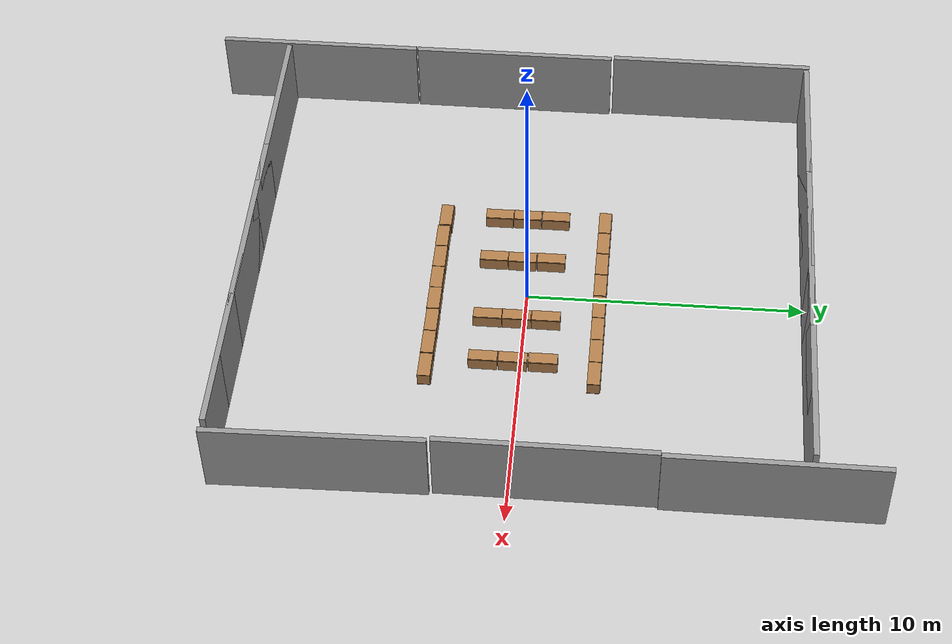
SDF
<sdf version="1.6">
 <world name="default">
  <light name="sun" type="directional">
   <pose>0 0 10 0 -0 0</pose>
   <diffuse>0.8 0.8 0.8 1</diffuse>
   <specular>0.1 0.1 0.1 1</specular>
   <attenuation>
    <range>1000</range>
    <constant>0.9</constant>
    <linear>0.01</linear>
    <quadratic>0.001</quadratic>
   </attenuation>
   <direction>-0.5 0.5 -1</direction>
  </light>
  <model name="ground_plane">
   <static>1</static>
   <link name="link">
    <collision name="collision">
     <geometry><plane><normal>0 0 1</normal><size>100 100</size></plane></geometry>
     <surface><friction><ode><mu>100</mu><mu2>50</mu2></ode></friction></surface>
    </collision>
    <visual name="visual">
     <cast_shadows>0</cast_shadows>
     <geometry><plane><normal>0 0 1</normal><size>100 100</size></plane></geometry>
     <material>
      <script><uri>file://media/materials/scripts/gazebo.material</uri><name>Gazebo/Grey</name></script>
     </material>
    </visual>
   </link>
  </model>
  <gravity>0 0 -9.8</gravity>
  <magnetic_field>6e-06 2.3e-05 -4.2e-05</magnetic_field>
  <atmosphere type="adiabatic"/>
  <physics name="default_physics" default="0" type="ode">
   <max_step_size>0.001</max_step_size>
   <real_time_factor>1</real_time_factor>
   <real_time_update_rate>1000</real_time_update_rate>
  </physics>
  <scene><ambient>0.4 0.4 0.4 1</ambient><background>0.7 0.7 0.7 1</background><shadows>1</shadows></scene>
  <spherical_coordinates>
   <surface_model>EARTH_WGS84</surface_model>
   <latitude_deg>0</latitude_deg>
   <longitude_deg>0</longitude_deg>
   <elevation>0</elevation>
   <heading_deg>0</heading_deg>
  </spherical_coordinates>
  <model name="grey_wall1_clone_0">
   <pose>-6.25 10 0 0 -0 0</pose>
   <static>1</static>
   <link name="grey_wall::link">
    <pose>0 0 1.4 0 -0 0</pose>
    <collision name="collision"><geometry><box><size>7.5 0.2 2.8</size></box></geometry></collision>
    <visual name="visual">
     <cast_shadows>0</cast_shadows>
     <geometry><box><size>7.5 0.2 2.8</size></box></geometry>
     <material>
      <script>
       <uri>model://grey_wall/materials/scripts</uri>
       <uri>model://grey_wall/materials/textures</uri>
       <name>vrc/grey_wall</name>
      </script>
     </material>
    </visual>
   </link>
  </model>
  <model name="grey_wall1_clone_1">
   <pose>-3.45 10 0 0 -0 0</pose>
   <static>1</static>
   <link name="grey_wall::link">
    <pose>0 0 1.4 0 -0 0</pose>
    <collision name="collision"><geometry><box><size>7.5 0.2 2.8</size></box></geometry></collision>
    <visual name="visual">
     <cast_shadows>0</cast_shadows>
     <geometry><box><size>7.5 0.2 2.8</size></box></geometry>
     <material>
      <script>
       <uri>model://grey_wall/materials/scripts</uri>
       <uri>model://grey_wall/materials/textures</uri>
       <name>vrc/grey_wall</name>
      </script>
     </material>
    </visual>
   </link>
  </model>
  <model name="grey_wall1_clone_2">
   <pose>-0.65 10 0 0 -0 0</pose>
   <static>1</static>
   <link name="grey_wall::link">
    <pose>0 0 1.4 0 -0 0</pose>
    <collision name="collision"><geometry><box><size>7.5 0.2 2.8</size></box></geometry></collision>
    <visual name="visual">
     <cast_shadows>0</cast_shadows>
     <geometry><box><size>7.5 0.2 2.8</size></box></geometry>
     <material>
      <script>
       <uri>model://grey_wall/materials/scripts</uri>
       <uri>model://grey_wall/materials/textures</uri>
       <name>vrc/grey_wall</name>
      </script>
     </material>
    </visual>
   </link>
  </model>
  <model name="grey_wall1_clone_3">
   <pose>2.15 10 0 0 -0 0</pose>
   <static>1</static>
   <link name="grey_wall::link">
    <pose>0 0 1.4 0 -0 0</pose>
    <collision name="collision"><geometry><box><size>7.5 0.2 2.8</size></box></geometry></collision>
    <visual name="visual">
     <cast_shadows>0</cast_shadows>
     <geometry><box><size>7.5 0.2 2.8</size></box></geometry>
     <material>
      <script>
       <uri>model://grey_wall/materials/scripts</uri>
       <uri>model://grey_wall/materials/textures</uri>
       <name>vrc/grey_wall</name>
      </script>
     </material>
    </visual>
   </link>
  </model>
  <model name="grey_wall1_clone_4">
   <pose>4.95 10 0 0 -0 0</pose>
   <static>1</static>
   <link name="grey_wall::link">
    <pose>0 0 1.4 0 -0 0</pose>
    <collision name="collision"><geometry><box><size>7.5 0.2 2.8</size></box></geometry></collision>
    <visual name="visual">
     <cast_shadows>0</cast_shadows>
     <geometry><box><size>7.5 0.2 2.8</size></box></geometry>
     <material>
      <script>
       <uri>model://grey_wall/materials/scripts</uri>
       <uri>model://grey_wall/materials/textures</uri>
       <name>vrc/grey_wall</name>
      </script>
     </material>
    </visual>
   </link>
  </model>
  <model name="grey_wall2_clone_0">
   <pose>-6.25 -10 0 0 -0 0</pose>
   <static>1</static>
   <link name="grey_wall::link">
    <pose>0 0 1.4 0 -0 0</pose>
    <collision name="collision"><geometry><box><size>7.5 0.2 2.8</size></box></geometry></collision>
    <visual name="visual">
     <cast_shadows>0</cast_shadows>
     <geometry><box><size>7.5 0.2 2.8</size></box></geometry>
     <material>
      <script>
       <uri>model://grey_wall/materials/scripts</uri>
       <uri>model://grey_wall/materials/textures</uri>
       <name>vrc/grey_wall</name>
      </script>
     </material>
    </visual>
   </link>
  </model>
  <model name="grey_wall2_clone_1">
   <pose>-3.45 -10 0 0 -0 0</pose>
   <static>1</static>
   <link name="grey_wall::link">
    <pose>0 0 1.4 0 -0 0</pose>
    <collision name="collision"><geometry><box><size>7.5 0.2 2.8</size></box></geometry></collision>
    <visual name="visual">
     <cast_shadows>0</cast_shadows>
     <geometry><box><size>7.5 0.2 2.8</size></box></geometry>
     <material>
      <script>
       <uri>model://grey_wall/materials/scripts</uri>
       <uri>model://grey_wall/materials/textures</uri>
       <name>vrc/grey_wall</name>
      </script>
     </material>
    </visual>
   </link>
  </model>
  <model name="grey_wall2_clone_2">
   <pose>-0.65 -10 0 0 -0 0</pose>
   <static>1</static>
   <link name="grey_wall::link">
    <pose>0 0 1.4 0 -0 0</pose>
    <collision name="collision"><geometry><box><size>7.5 0.2 2.8</size></box></geometry></collision>
    <visual name="visual">
     <cast_shadows>0</cast_shadows>
     <geometry><box><size>7.5 0.2 2.8</size></box></geometry>
     <material>
      <script>
       <uri>model://grey_wall/materials/scripts</uri>
       <uri>model://grey_wall/materials/textures</uri>
       <name>vrc/grey_wall</name>
      </script>
     </material>
    </visual>
   </link>
  </model>
  <model name="grey_wall2_clone_3">
   <pose>2.15 -10 0 0 -0 0</pose>
   <static>1</static>
   <link name="grey_wall::link">
    <pose>0 0 1.4 0 -0 0</pose>
    <collision name="collision"><geometry><box><size>7.5 0.2 2.8</size></box></geometry></collision>
    <visual name="visual">
     <cast_shadows>0</cast_shadows>
     <geometry><box><size>7.5 0.2 2.8</size></box></geometry>
     <material>
      <script>
       <uri>model://grey_wall/materials/scripts</uri>
       <uri>model://grey_wall/materials/textures</uri>
       <name>vrc/grey_wall</name>
      </script>
     </material>
    </visual>
   </link>
  </model>
  <model name="grey_wall2_clone_4">
   <pose>4.95 -10 0 0 -0 0</pose>
   <static>1</static>
   <link name="grey_wall::link">
    <pose>0 0 1.4 0 -0 0</pose>
    <collision name="collision"><geometry><box><size>7.5 0.2 2.8</size></box></geometry></collision>
    <visual name="visual">
     <cast_shadows>0</cast_shadows>
     <geometry><box><size>7.5 0.2 2.8</size></box></geometry>
     <material>
      <script>
       <uri>model://grey_wall/materials/scripts</uri>
       <uri>model://grey_wall/materials/textures</uri>
       <name>vrc/grey_wall</name>
      </script>
     </material>
    </visual>
   </link>
  </model>
  <model name="grey_wall">
   <static>1</static>
   <link name="link">
    <pose>0 0 1.4 0 -0 0</pose>
    <collision name="collision"><geometry><box><size>7.5 0.2 2.8</size></box></geometry></collision>
    <visual name="visual">
     <cast_shadows>0</cast_shadows>
     <geometry><box><size>7.5 0.2 2.8</size></box></geometry>
     <material>
      <script>
       <uri>model://grey_wall/materials/scripts</uri>
       <uri>model://grey_wall/materials/textures</uri>
       <name>vrc/grey_wall</name>
      </script>
     </material>
    </visual>
   </link>
   <pose>9.06574 -6.3529 0 0 -0 1.58406</pose>
  </model>
  <model name="grey_wall_clone">
   <static>1</static>
   <link name="link">
    <pose>0 0 1.4 0 -0 0</pose>
    <collision name="collision"><geometry><box><size>7.5 0.2 2.8</size></box></geometry></collision>
    <visual name="visual">
     <cast_shadows>0</cast_shadows>
     <geometry><box><size>7.5 0.2 2.8</size></box></geometry>
     <material>
      <script>
       <uri>model://grey_wall/materials/scripts</uri>
       <uri>model://grey_wall/materials/textures</uri>
       <name>vrc/grey_wall</name>
      </script>
     </material>
    </visual>
   </link>
   <pose>8.95683 1.2518 0 0 -0 1.5647</pose>
  </model>
  <model name="grey_wall_clone_clone">
   <static>1</static>
   <link name="link">
    <pose>0 0 1.4 0 -0 0</pose>
    <collision name="collision"><geometry><box><size>7.5 0.2 2.8</size></box></geometry></collision>
    <visual name="visual">
     <cast_shadows>0</cast_shadows>
     <geometry><box><size>7.5 0.2 2.8</size></box></geometry>
     <material>
      <script>
       <uri>model://grey_wall/materials/scripts</uri>
       <uri>model://grey_wall/materials/textures</uri>
       <name>vrc/grey_wall</name>
      </script>
     </material>
    </visual>
   </link>
   <pose>9.08981 8.7681 0 0 -0 1.5647</pose>
  </model>
  <model name="grey_wall_clone_clone_clone">
   <static>1</static>
   <link name="link">
    <pose>0 0 1.4 0 -0 0</pose>
    <collision name="collision"><geometry><box><size>7.5 0.2 2.8</size></box></geometry></collision>
    <visual name="visual">
     <cast_shadows>0</cast_shadows>
     <geometry><box><size>7.5 0.2 2.8</size></box></geometry>
     <material>
      <script>
       <uri>model://grey_wall/materials/scripts</uri>
       <uri>model://grey_wall/materials/textures</uri>
       <name>vrc/grey_wall</name>
      </script>
     </material>
    </visual>
   </link>
   <pose>-10.1653 6.35833 0 0 -0 1.5647</pose>
  </model>
  <model name="grey_wall_clone_clone_clone_clone">
   <static>1</static>
   <link name="link">
    <pose>0 0 1.4 0 -0 0</pose>
    <collision name="collision"><geometry><box><size>7.5 0.2 2.8</size></box></geometry></collision>
    <visual name="visual">
     <cast_shadows>0</cast_shadows>
     <geometry><box><size>7.5 0.2 2.8</size></box></geometry>
     <material>
      <script>
       <uri>model://grey_wall/materials/scripts</uri>
       <uri>model://grey_wall/materials/textures</uri>
       <name>vrc/grey_wall</name>
      </script>
     </material>
    </visual>
   </link>
   <pose>-10.1357 -1.24273 0 0 -0 1.5647</pose>
  </model>
  <model name="grey_wall_clone_clone_clone_clone_0">
   <static>1</static>
   <link name="link">
    <pose>0 0 1.4 0 -0 0</pose>
    <collision name="collision"><geometry><box><size>7.5 0.2 2.8</size></box></geometry></collision>
    <visual name="visual">
     <cast_shadows>0</cast_shadows>
     <geometry><box><size>7.5 0.2 2.8</size></box></geometry>
     <material>
      <script>
       <uri>model://grey_wall/materials/scripts</uri>
       <uri>model://grey_wall/materials/textures</uri>
       <name>vrc/grey_wall</name>
      </script>
     </material>
    </visual>
   </link>
   <pose>-10.1848 -8.80836 0 0 -0 1.5647</pose>
  </model>
  <model name="cabinet">
   <static>1</static>
   <link name="cabinet_bottom_plate">
    <inertial>
     <pose>0 0 -1 0 -0 0</pose>
     <inertia><ixx>2.05</ixx><ixy>0</ixy><ixz>0</ixz><iyy>2.05</iyy><iyz>0</iyz><izz>2.05</izz></inertia>
     <mass>25</mass>
    </inertial>
    <collision name="cabinet_bottom_plate_geom">
     <pose>0 0 0.01 0 -0 0</pose>
     <geometry><box><size>0.45 0.45 0.02</size></box></geometry>
    </collision>
    <visual name="cabinet_bottom_plate_geom_visual">
     <pose>0 0 0.01 0 -0 0</pose>
     <geometry><box><size>0.45 0.45 0.02</size></box></geometry>
     <material>
      <script><uri>file://media/materials/scripts/gazebo.material</uri><name>Gazebo/Wood</name></script>
     </material>
    </visual>
    <collision name="cabinet_bottom_plate_geom_cabinet_back_plate">
     <pose>0.235 0 0.51 0 -0 0</pose>
     <geometry><box><size>0.02 0.45 1.02</size></box></geometry>
    </collision>
    <visual name="cabinet_bottom_plate_geom_cabinet_back_plate_visual">
     <pose>0.235 0 0.51 0 -0 0</pose>
     <geometry><box><size>0.02 0.45 1.02</size></box></geometry>
     <material>
      <script><uri>file://media/materials/scripts/gazebo.material</uri><name>Gazebo/Wood</name></script>
     </material>
    </visual>
    <collision name="cabinet_bottom_plate_geom_cabinet_left_plate">
     <pose>0 0.235 0.51 0 -0 0</pose>
     <geometry><box><size>0.45 0.02 1.02</size></box></geometry>
    </collision>
    <visual name="cabinet_bottom_plate_geom_cabinet_left_plate_visual">
     <pose>0 0.235 0.51 0 -0 0</pose>
     <geometry><box><size>0.45 0.02 1.02</size></box></geometry>
     <material>
      <script><uri>file://media/materials/scripts/gazebo.material</uri><name>Gazebo/Wood</name></script>
     </material>
    </visual>
    <collision name="cabinet_bottom_plate_geom_cabinet_middle_plate">
     <pose>0 0 0.51 0 -0 0</pose>
     <geometry><box><size>0.45 0.45 0.02</size></box></geometry>
    </collision>
    <visual name="cabinet_bottom_plate_geom_cabinet_middle_plate_visual">
     <pose>0 0 0.51 0 -0 0</pose>
     <geometry><box><size>0.45 0.45 0.02</size></box></geometry>
     <material>
      <script><uri>file://media/materials/scripts/gazebo.material</uri><name>Gazebo/Wood</name></script>
     </material>
    </visual>
    <collision name="cabinet_bottom_plate_geom_cabinet_right_plate">
     <pose>0 -0.235 0.51 0 -0 0</pose>
     <geometry><box><size>0.45 0.02 1.02</size></box></geometry>
    </collision>
    <visual name="cabinet_bottom_plate_geom_cabinet_right_plate_visual">
     <pose>0 -0.235 0.51 0 -0 0</pose>
     <geometry><box><size>0.45 0.02 1.02</size></box></geometry>
     <material>
      <script><uri>file://media/materials/scripts/gazebo.material</uri><name>Gazebo/Wood</name></script>
     </material>
    </visual>
    <collision name="cabinet_bottom_plate_geom_cabinet_top_plate">
     <pose>0 0 1.01 0 -0 0</pose>
     <geometry><box><size>0.45 0.45 0.02</size></box></geometry>
    </collision>
    <visual name="cabinet_bottom_plate_geom_cabinet_top_plate_visual">
     <pose>0 0 1.01 0 -0 0</pose>
     <geometry><box><size>0.45 0.45 0.02</size></box></geometry>
     <material>
      <script><uri>file://media/materials/scripts/gazebo.material</uri><name>Gazebo/Wood</name></script>
     </material>
    </visual>
   </link>
   <pose>3.29168 0.29942 0.264462 -1.57506 0 0</pose>
  </model>
  <model name="cabinet_clone">
   <static>1</static>
   <link name="cabinet_bottom_plate">
    <inertial>
     <pose>0 0 -1 0 -0 0</pose>
     <inertia><ixx>2.05</ixx><ixy>0</ixy><ixz>0</ixz><iyy>2.05</iyy><iyz>0</iyz><izz>2.05</izz></inertia>
     <mass>25</mass>
    </inertial>
    <collision name="cabinet_bottom_plate_geom">
     <pose>0 0 0.01 0 -0 0</pose>
     <geometry><box><size>0.45 0.45 0.02</size></box></geometry>
    </collision>
    <visual name="cabinet_bottom_plate_geom_visual">
     <pose>0 0 0.01 0 -0 0</pose>
     <geometry><box><size>0.45 0.45 0.02</size></box></geometry>
     <material>
      <script><uri>file://media/materials/scripts/gazebo.material</uri><name>Gazebo/Wood</name></script>
     </material>
    </visual>
    <collision name="cabinet_bottom_plate_geom_cabinet_back_plate">
     <pose>0.235 0 0.51 0 -0 0</pose>
     <geometry><box><size>0.02 0.45 1.02</size></box></geometry>
    </collision>
    <visual name="cabinet_bottom_plate_geom_cabinet_back_plate_visual">
     <pose>0.235 0 0.51 0 -0 0</pose>
     <geometry><box><size>0.02 0.45 1.02</size></box></geometry>
     <material>
      <script><uri>file://media/materials/scripts/gazebo.material</uri><name>Gazebo/Wood</name></script>
     </material>
    </visual>
    <collision name="cabinet_bottom_plate_geom_cabinet_left_plate">
     <pose>0 0.235 0.51 0 -0 0</pose>
     <geometry><box><size>0.45 0.02 1.02</size></box></geometry>
    </collision>
    <visual name="cabinet_bottom_plate_geom_cabinet_left_plate_visual">
     <pose>0 0.235 0.51 0 -0 0</pose>
     <geometry><box><size>0.45 0.02 1.02</size></box></geometry>
     <material>
      <script><uri>file://media/materials/scripts/gazebo.material</uri><name>Gazebo/Wood</name></script>
     </material>
    </visual>
    <collision name="cabinet_bottom_plate_geom_cabinet_middle_plate">
     <pose>0 0 0.51 0 -0 0</pose>
     <geometry><box><size>0.45 0.45 0.02</size></box></geometry>
    </collision>
    <visual name="cabinet_bottom_plate_geom_cabinet_middle_plate_visual">
     <pose>0 0 0.51 0 -0 0</pose>
     <geometry><box><size>0.45 0.45 0.02</size></box></geometry>
     <material>
      <script><uri>file://media/materials/scripts/gazebo.material</uri><name>Gazebo/Wood</name></script>
     </material>
    </visual>
    <collision name="cabinet_bottom_plate_geom_cabinet_right_plate">
     <pose>0 -0.235 0.51 0 -0 0</pose>
     <geometry><box><size>0.45 0.02 1.02</size></box></geometry>
    </collision>
    <visual name="cabinet_bottom_plate_geom_cabinet_right_plate_visual">
     <pose>0 -0.235 0.51 0 -0 0</pose>
     <geometry><box><size>0.45 0.02 1.02</size></box></geometry>
     <material>
      <script><uri>file://media/materials/scripts/gazebo.material</uri><name>Gazebo/Wood</name></script>
     </material>
    </visual>
    <collision name="cabinet_bottom_plate_geom_cabinet_top_plate">
     <pose>0 0 1.01 0 -0 0</pose>
     <geometry><box><size>0.45 0.45 0.02</size></box></geometry>
    </collision>
    <visual name="cabinet_bottom_plate_geom_cabinet_top_plate_visual">
     <pose>0 0 1.01 0 -0 0</pose>
     <geometry><box><size>0.45 0.45 0.02</size></box></geometry>
     <material>
      <script><uri>file://media/materials/scripts/gazebo.material</uri><name>Gazebo/Wood</name></script>
     </material>
    </visual>
   </link>
   <pose>3.30353 -0.766856 0.264462 -1.57506 0 0</pose>
  </model>
  <model name="cabinet_clone_0">
   <static>1</static>
   <link name="cabinet_bottom_plate">
    <inertial>
     <pose>0 0 -1 0 -0 0</pose>
     <inertia><ixx>2.05</ixx><ixy>0</ixy><ixz>0</ixz><iyy>2.05</iyy><iyz>0</iyz><izz>2.05</izz></inertia>
     <mass>25</mass>
    </inertial>
    <collision name="cabinet_bottom_plate_geom">
     <pose>0 0 0.01 0 -0 0</pose>
     <geometry><box><size>0.45 0.45 0.02</size></box></geometry>
    </collision>
    <visual name="cabinet_bottom_plate_geom_visual">
     <pose>0 0 0.01 0 -0 0</pose>
     <geometry><box><size>0.45 0.45 0.02</size></box></geometry>
     <material>
      <script><uri>file://media/materials/scripts/gazebo.material</uri><name>Gazebo/Wood</name></script>
     </material>
    </visual>
    <collision name="cabinet_bottom_plate_geom_cabinet_back_plate">
     <pose>0.235 0 0.51 0 -0 0</pose>
     <geometry><box><size>0.02 0.45 1.02</size></box></geometry>
    </collision>
    <visual name="cabinet_bottom_plate_geom_cabinet_back_plate_visual">
     <pose>0.235 0 0.51 0 -0 0</pose>
     <geometry><box><size>0.02 0.45 1.02</size></box></geometry>
     <material>
      <script><uri>file://media/materials/scripts/gazebo.material</uri><name>Gazebo/Wood</name></script>
     </material>
    </visual>
    <collision name="cabinet_bottom_plate_geom_cabinet_left_plate">
     <pose>0 0.235 0.51 0 -0 0</pose>
     <geometry><box><size>0.45 0.02 1.02</size></box></geometry>
    </collision>
    <visual name="cabinet_bottom_plate_geom_cabinet_left_plate_visual">
     <pose>0 0.235 0.51 0 -0 0</pose>
     <geometry><box><size>0.45 0.02 1.02</size></box></geometry>
     <material>
      <script><uri>file://media/materials/scripts/gazebo.material</uri><name>Gazebo/Wood</name></script>
     </material>
    </visual>
    <collision name="cabinet_bottom_plate_geom_cabinet_middle_plate">
     <pose>0 0 0.51 0 -0 0</pose>
     <geometry><box><size>0.45 0.45 0.02</size></box></geometry>
    </collision>
    <visual name="cabinet_bottom_plate_geom_cabinet_middle_plate_visual">
     <pose>0 0 0.51 0 -0 0</pose>
     <geometry><box><size>0.45 0.45 0.02</size></box></geometry>
     <material>
      <script><uri>file://media/materials/scripts/gazebo.material</uri><name>Gazebo/Wood</name></script>
     </material>
    </visual>
    <collision name="cabinet_bottom_plate_geom_cabinet_right_plate">
     <pose>0 -0.235 0.51 0 -0 0</pose>
     <geometry><box><size>0.45 0.02 1.02</size></box></geometry>
    </collision>
    <visual name="cabinet_bottom_plate_geom_cabinet_right_plate_visual">
     <pose>0 -0.235 0.51 0 -0 0</pose>
     <geometry><box><size>0.45 0.02 1.02</size></box></geometry>
     <material>
      <script><uri>file://media/materials/scripts/gazebo.material</uri><name>Gazebo/Wood</name></script>
     </material>
    </visual>
    <collision name="cabinet_bottom_plate_geom_cabinet_top_plate">
     <pose>0 0 1.01 0 -0 0</pose>
     <geometry><box><size>0.45 0.45 0.02</size></box></geometry>
    </collision>
    <visual name="cabinet_bottom_plate_geom_cabinet_top_plate_visual">
     <pose>0 0 1.01 0 -0 0</pose>
     <geometry><box><size>0.45 0.45 0.02</size></box></geometry>
     <material>
      <script><uri>file://media/materials/scripts/gazebo.material</uri><name>Gazebo/Wood</name></script>
     </material>
    </visual>
   </link>
   <pose>3.2968 -1.82483 0.264462 -1.57506 0 0</pose>
  </model>
  <model name="cabinet_clone_1">
   <static>1</static>
   <link name="cabinet_bottom_plate">
    <inertial>
     <pose>0 0 -1 0 -0 0</pose>
     <inertia><ixx>2.05</ixx><ixy>0</ixy><ixz>0</ixz><iyy>2.05</iyy><iyz>0</iyz><izz>2.05</izz></inertia>
     <mass>25</mass>
    </inertial>
    <collision name="cabinet_bottom_plate_geom">
     <pose>0 0 0.01 0 -0 0</pose>
     <geometry><box><size>0.45 0.45 0.02</size></box></geometry>
    </collision>
    <visual name="cabinet_bottom_plate_geom_visual">
     <pose>0 0 0.01 0 -0 0</pose>
     <geometry><box><size>0.45 0.45 0.02</size></box></geometry>
     <material>
      <script><uri>file://media/materials/scripts/gazebo.material</uri><name>Gazebo/Wood</name></script>
     </material>
    </visual>
    <collision name="cabinet_bottom_plate_geom_cabinet_back_plate">
     <pose>0.235 0 0.51 0 -0 0</pose>
     <geometry><box><size>0.02 0.45 1.02</size></box></geometry>
    </collision>
    <visual name="cabinet_bottom_plate_geom_cabinet_back_plate_visual">
     <pose>0.235 0 0.51 0 -0 0</pose>
     <geometry><box><size>0.02 0.45 1.02</size></box></geometry>
     <material>
      <script><uri>file://media/materials/scripts/gazebo.material</uri><name>Gazebo/Wood</name></script>
     </material>
    </visual>
    <collision name="cabinet_bottom_plate_geom_cabinet_left_plate">
     <pose>0 0.235 0.51 0 -0 0</pose>
     <geometry><box><size>0.45 0.02 1.02</size></box></geometry>
    </collision>
    <visual name="cabinet_bottom_plate_geom_cabinet_left_plate_visual">
     <pose>0 0.235 0.51 0 -0 0</pose>
     <geometry><box><size>0.45 0.02 1.02</size></box></geometry>
     <material>
      <script><uri>file://media/materials/scripts/gazebo.material</uri><name>Gazebo/Wood</name></script>
     </material>
    </visual>
    <collision name="cabinet_bottom_plate_geom_cabinet_middle_plate">
     <pose>0 0 0.51 0 -0 0</pose>
     <geometry><box><size>0.45 0.45 0.02</size></box></geometry>
    </collision>
    <visual name="cabinet_bottom_plate_geom_cabinet_middle_plate_visual">
     <pose>0 0 0.51 0 -0 0</pose>
     <geometry><box><size>0.45 0.45 0.02</size></box></geometry>
     <material>
      <script><uri>file://media/materials/scripts/gazebo.material</uri><name>Gazebo/Wood</name></script>
     </material>
    </visual>
    <collision name="cabinet_bottom_plate_geom_cabinet_right_plate">
     <pose>0 -0.235 0.51 0 -0 0</pose>
     <geometry><box><size>0.45 0.02 1.02</size></box></geometry>
    </collision>
    <visual name="cabinet_bottom_plate_geom_cabinet_right_plate_visual">
     <pose>0 -0.235 0.51 0 -0 0</pose>
     <geometry><box><size>0.45 0.02 1.02</size></box></geometry>
     <material>
      <script><uri>file://media/materials/scripts/gazebo.material</uri><name>Gazebo/Wood</name></script>
     </material>
    </visual>
    <collision name="cabinet_bottom_plate_geom_cabinet_top_plate">
     <pose>0 0 1.01 0 -0 0</pose>
     <geometry><box><size>0.45 0.45 0.02</size></box></geometry>
    </collision>
    <visual name="cabinet_bottom_plate_geom_cabinet_top_plate_visual">
     <pose>0 0 1.01 0 -0 0</pose>
     <geometry><box><size>0.45 0.45 0.02</size></box></geometry>
     <material>
      <script><uri>file://media/materials/scripts/gazebo.material</uri><name>Gazebo/Wood</name></script>
     </material>
    </visual>
   </link>
   <pose>1.29788 0.265843 0.264462 -1.57506 0 0</pose>
  </model>
  <model name="cabinet_clone_2">
   <static>1</static>
   <link name="cabinet_bottom_plate">
    <inertial>
     <pose>0 0 -1 0 -0 0</pose>
     <inertia><ixx>2.05</ixx><ixy>0</ixy><ixz>0</ixz><iyy>2.05</iyy><iyz>0</iyz><izz>2.05</izz></inertia>
     <mass>25</mass>
    </inertial>
    <collision name="cabinet_bottom_plate_geom">
     <pose>0 0 0.01 0 -0 0</pose>
     <geometry><box><size>0.45 0.45 0.02</size></box></geometry>
    </collision>
    <visual name="cabinet_bottom_plate_geom_visual">
     <pose>0 0 0.01 0 -0 0</pose>
     <geometry><box><size>0.45 0.45 0.02</size></box></geometry>
     <material>
      <script><uri>file://media/materials/scripts/gazebo.material</uri><name>Gazebo/Wood</name></script>
     </material>
    </visual>
    <collision name="cabinet_bottom_plate_geom_cabinet_back_plate">
     <pose>0.235 0 0.51 0 -0 0</pose>
     <geometry><box><size>0.02 0.45 1.02</size></box></geometry>
    </collision>
    <visual name="cabinet_bottom_plate_geom_cabinet_back_plate_visual">
     <pose>0.235 0 0.51 0 -0 0</pose>
     <geometry><box><size>0.02 0.45 1.02</size></box></geometry>
     <material>
      <script><uri>file://media/materials/scripts/gazebo.material</uri><name>Gazebo/Wood</name></script>
     </material>
    </visual>
    <collision name="cabinet_bottom_plate_geom_cabinet_left_plate">
     <pose>0 0.235 0.51 0 -0 0</pose>
     <geometry><box><size>0.45 0.02 1.02</size></box></geometry>
    </collision>
    <visual name="cabinet_bottom_plate_geom_cabinet_left_plate_visual">
     <pose>0 0.235 0.51 0 -0 0</pose>
     <geometry><box><size>0.45 0.02 1.02</size></box></geometry>
     <material>
      <script><uri>file://media/materials/scripts/gazebo.material</uri><name>Gazebo/Wood</name></script>
     </material>
    </visual>
    <collision name="cabinet_bottom_plate_geom_cabinet_middle_plate">
     <pose>0 0 0.51 0 -0 0</pose>
     <geometry><box><size>0.45 0.45 0.02</size></box></geometry>
    </collision>
    <visual name="cabinet_bottom_plate_geom_cabinet_middle_plate_visual">
     <pose>0 0 0.51 0 -0 0</pose>
     <geometry><box><size>0.45 0.45 0.02</size></box></geometry>
     <material>
      <script><uri>file://media/materials/scripts/gazebo.material</uri><name>Gazebo/Wood</name></script>
     </material>
    </visual>
    <collision name="cabinet_bottom_plate_geom_cabinet_right_plate">
     <pose>0 -0.235 0.51 0 -0 0</pose>
     <geometry><box><size>0.45 0.02 1.02</size></box></geometry>
    </collision>
    <visual name="cabinet_bottom_plate_geom_cabinet_right_plate_visual">
     <pose>0 -0.235 0.51 0 -0 0</pose>
     <geometry><box><size>0.45 0.02 1.02</size></box></geometry>
     <material>
      <script><uri>file://media/materials/scripts/gazebo.material</uri><name>Gazebo/Wood</name></script>
     </material>
    </visual>
    <collision name="cabinet_bottom_plate_geom_cabinet_top_plate">
     <pose>0 0 1.01 0 -0 0</pose>
     <geometry><box><size>0.45 0.45 0.02</size></box></geometry>
    </collision>
    <visual name="cabinet_bottom_plate_geom_cabinet_top_plate_visual">
     <pose>0 0 1.01 0 -0 0</pose>
     <geometry><box><size>0.45 0.45 0.02</size></box></geometry>
     <material>
      <script><uri>file://media/materials/scripts/gazebo.material</uri><name>Gazebo/Wood</name></script>
     </material>
    </visual>
   </link>
   <pose>1.29879 -0.786258 0.264462 -1.57506 0 0</pose>
  </model>
  <model name="cabinet_clone_3">
   <static>1</static>
   <link name="cabinet_bottom_plate">
    <inertial>
     <pose>0 0 -1 0 -0 0</pose>
     <inertia><ixx>2.05</ixx><ixy>0</ixy><ixz>0</ixz><iyy>2.05</iyy><iyz>0</iyz><izz>2.05</izz></inertia>
     <mass>25</mass>
    </inertial>
    <collision name="cabinet_bottom_plate_geom">
     <pose>0 0 0.01 0 -0 0</pose>
     <geometry><box><size>0.45 0.45 0.02</size></box></geometry>
    </collision>
    <visual name="cabinet_bottom_plate_geom_visual">
     <pose>0 0 0.01 0 -0 0</pose>
     <geometry><box><size>0.45 0.45 0.02</size></box></geometry>
     <material>
      <script><uri>file://media/materials/scripts/gazebo.material</uri><name>Gazebo/Wood</name></script>
     </material>
    </visual>
    <collision name="cabinet_bottom_plate_geom_cabinet_back_plate">
     <pose>0.235 0 0.51 0 -0 0</pose>
     <geometry><box><size>0.02 0.45 1.02</size></box></geometry>
    </collision>
    <visual name="cabinet_bottom_plate_geom_cabinet_back_plate_visual">
     <pose>0.235 0 0.51 0 -0 0</pose>
     <geometry><box><size>0.02 0.45 1.02</size></box></geometry>
     <material>
      <script><uri>file://media/materials/scripts/gazebo.material</uri><name>Gazebo/Wood</name></script>
     </material>
    </visual>
    <collision name="cabinet_bottom_plate_geom_cabinet_left_plate">
     <pose>0 0.235 0.51 0 -0 0</pose>
     <geometry><box><size>0.45 0.02 1.02</size></box></geometry>
    </collision>
    <visual name="cabinet_bottom_plate_geom_cabinet_left_plate_visual">
     <pose>0 0.235 0.51 0 -0 0</pose>
     <geometry><box><size>0.45 0.02 1.02</size></box></geometry>
     <material>
      <script><uri>file://media/materials/scripts/gazebo.material</uri><name>Gazebo/Wood</name></script>
     </material>
    </visual>
    <collision name="cabinet_bottom_plate_geom_cabinet_middle_plate">
     <pose>0 0 0.51 0 -0 0</pose>
     <geometry><box><size>0.45 0.45 0.02</size></box></geometry>
    </collision>
    <visual name="cabinet_bottom_plate_geom_cabinet_middle_plate_visual">
     <pose>0 0 0.51 0 -0 0</pose>
     <geometry><box><size>0.45 0.45 0.02</size></box></geometry>
     <material>
      <script><uri>file://media/materials/scripts/gazebo.material</uri><name>Gazebo/Wood</name></script>
     </material>
    </visual>
    <collision name="cabinet_bottom_plate_geom_cabinet_right_plate">
     <pose>0 -0.235 0.51 0 -0 0</pose>
     <geometry><box><size>0.45 0.02 1.02</size></box></geometry>
    </collision>
    <visual name="cabinet_bottom_plate_geom_cabinet_right_plate_visual">
     <pose>0 -0.235 0.51 0 -0 0</pose>
     <geometry><box><size>0.45 0.02 1.02</size></box></geometry>
     <material>
      <script><uri>file://media/materials/scripts/gazebo.material</uri><name>Gazebo/Wood</name></script>
     </material>
    </visual>
    <collision name="cabinet_bottom_plate_geom_cabinet_top_plate">
     <pose>0 0 1.01 0 -0 0</pose>
     <geometry><box><size>0.45 0.45 0.02</size></box></geometry>
    </collision>
    <visual name="cabinet_bottom_plate_geom_cabinet_top_plate_visual">
     <pose>0 0 1.01 0 -0 0</pose>
     <geometry><box><size>0.45 0.45 0.02</size></box></geometry>
     <material>
      <script><uri>file://media/materials/scripts/gazebo.material</uri><name>Gazebo/Wood</name></script>
     </material>
    </visual>
   </link>
   <pose>1.30027 -1.829 0.264462 -1.57506 0 0</pose>
  </model>
  <model name="cabinet_clone_4">
   <static>1</static>
   <link name="cabinet_bottom_plate">
    <inertial>
     <pose>0 0 -1 0 -0 0</pose>
     <inertia><ixx>2.05</ixx><ixy>0</ixy><ixz>0</ixz><iyy>2.05</iyy><iyz>0</iyz><izz>2.05</izz></inertia>
     <mass>25</mass>
    </inertial>
    <collision name="cabinet_bottom_plate_geom">
     <pose>0 0 0.01 0 -0 0</pose>
     <geometry><box><size>0.45 0.45 0.02</size></box></geometry>
    </collision>
    <visual name="cabinet_bottom_plate_geom_visual">
     <pose>0 0 0.01 0 -0 0</pose>
     <geometry><box><size>0.45 0.45 0.02</size></box></geometry>
     <material>
      <script><uri>file://media/materials/scripts/gazebo.material</uri><name>Gazebo/Wood</name></script>
     </material>
    </visual>
    <collision name="cabinet_bottom_plate_geom_cabinet_back_plate">
     <pose>0.235 0 0.51 0 -0 0</pose>
     <geometry><box><size>0.02 0.45 1.02</size></box></geometry>
    </collision>
    <visual name="cabinet_bottom_plate_geom_cabinet_back_plate_visual">
     <pose>0.235 0 0.51 0 -0 0</pose>
     <geometry><box><size>0.02 0.45 1.02</size></box></geometry>
     <material>
      <script><uri>file://media/materials/scripts/gazebo.material</uri><name>Gazebo/Wood</name></script>
     </material>
    </visual>
    <collision name="cabinet_bottom_plate_geom_cabinet_left_plate">
     <pose>0 0.235 0.51 0 -0 0</pose>
     <geometry><box><size>0.45 0.02 1.02</size></box></geometry>
    </collision>
    <visual name="cabinet_bottom_plate_geom_cabinet_left_plate_visual">
     <pose>0 0.235 0.51 0 -0 0</pose>
     <geometry><box><size>0.45 0.02 1.02</size></box></geometry>
     <material>
      <script><uri>file://media/materials/scripts/gazebo.material</uri><name>Gazebo/Wood</name></script>
     </material>
    </visual>
    <collision name="cabinet_bottom_plate_geom_cabinet_middle_plate">
     <pose>0 0 0.51 0 -0 0</pose>
     <geometry><box><size>0.45 0.45 0.02</size></box></geometry>
    </collision>
    <visual name="cabinet_bottom_plate_geom_cabinet_middle_plate_visual">
     <pose>0 0 0.51 0 -0 0</pose>
     <geometry><box><size>0.45 0.45 0.02</size></box></geometry>
     <material>
      <script><uri>file://media/materials/scripts/gazebo.material</uri><name>Gazebo/Wood</name></script>
     </material>
    </visual>
    <collision name="cabinet_bottom_plate_geom_cabinet_right_plate">
     <pose>0 -0.235 0.51 0 -0 0</pose>
     <geometry><box><size>0.45 0.02 1.02</size></box></geometry>
    </collision>
    <visual name="cabinet_bottom_plate_geom_cabinet_right_plate_visual">
     <pose>0 -0.235 0.51 0 -0 0</pose>
     <geometry><box><size>0.45 0.02 1.02</size></box></geometry>
     <material>
      <script><uri>file://media/materials/scripts/gazebo.material</uri><name>Gazebo/Wood</name></script>
     </material>
    </visual>
    <collision name="cabinet_bottom_plate_geom_cabinet_top_plate">
     <pose>0 0 1.01 0 -0 0</pose>
     <geometry><box><size>0.45 0.45 0.02</size></box></geometry>
    </collision>
    <visual name="cabinet_bottom_plate_geom_cabinet_top_plate_visual">
     <pose>0 0 1.01 0 -0 0</pose>
     <geometry><box><size>0.45 0.45 0.02</size></box></geometry>
     <material>
      <script><uri>file://media/materials/scripts/gazebo.material</uri><name>Gazebo/Wood</name></script>
     </material>
    </visual>
   </link>
   <pose>-1.53952 0.268414 0.264462 -1.57506 0 0</pose>
  </model>
  <model name="cabinet_clone_5">
   <static>1</static>
   <link name="cabinet_bottom_plate">
    <inertial>
     <pose>0 0 -1 0 -0 0</pose>
     <inertia><ixx>2.05</ixx><ixy>0</ixy><ixz>0</ixz><iyy>2.05</iyy><iyz>0</iyz><izz>2.05</izz></inertia>
     <mass>25</mass>
    </inertial>
    <collision name="cabinet_bottom_plate_geom">
     <pose>0 0 0.01 0 -0 0</pose>
     <geometry><box><size>0.45 0.45 0.02</size></box></geometry>
    </collision>
    <visual name="cabinet_bottom_plate_geom_visual">
     <pose>0 0 0.01 0 -0 0</pose>
     <geometry><box><size>0.45 0.45 0.02</size></box></geometry>
     <material>
      <script><uri>file://media/materials/scripts/gazebo.material</uri><name>Gazebo/Wood</name></script>
     </material>
    </visual>
    <collision name="cabinet_bottom_plate_geom_cabinet_back_plate">
     <pose>0.235 0 0.51 0 -0 0</pose>
     <geometry><box><size>0.02 0.45 1.02</size></box></geometry>
    </collision>
    <visual name="cabinet_bottom_plate_geom_cabinet_back_plate_visual">
     <pose>0.235 0 0.51 0 -0 0</pose>
     <geometry><box><size>0.02 0.45 1.02</size></box></geometry>
     <material>
      <script><uri>file://media/materials/scripts/gazebo.material</uri><name>Gazebo/Wood</name></script>
     </material>
    </visual>
    <collision name="cabinet_bottom_plate_geom_cabinet_left_plate">
     <pose>0 0.235 0.51 0 -0 0</pose>
     <geometry><box><size>0.45 0.02 1.02</size></box></geometry>
    </collision>
    <visual name="cabinet_bottom_plate_geom_cabinet_left_plate_visual">
     <pose>0 0.235 0.51 0 -0 0</pose>
     <geometry><box><size>0.45 0.02 1.02</size></box></geometry>
     <material>
      <script><uri>file://media/materials/scripts/gazebo.material</uri><name>Gazebo/Wood</name></script>
     </material>
    </visual>
    <collision name="cabinet_bottom_plate_geom_cabinet_middle_plate">
     <pose>0 0 0.51 0 -0 0</pose>
     <geometry><box><size>0.45 0.45 0.02</size></box></geometry>
    </collision>
    <visual name="cabinet_bottom_plate_geom_cabinet_middle_plate_visual">
     <pose>0 0 0.51 0 -0 0</pose>
     <geometry><box><size>0.45 0.45 0.02</size></box></geometry>
     <material>
      <script><uri>file://media/materials/scripts/gazebo.material</uri><name>Gazebo/Wood</name></script>
     </material>
    </visual>
    <collision name="cabinet_bottom_plate_geom_cabinet_right_plate">
     <pose>0 -0.235 0.51 0 -0 0</pose>
     <geometry><box><size>0.45 0.02 1.02</size></box></geometry>
    </collision>
    <visual name="cabinet_bottom_plate_geom_cabinet_right_plate_visual">
     <pose>0 -0.235 0.51 0 -0 0</pose>
     <geometry><box><size>0.45 0.02 1.02</size></box></geometry>
     <material>
      <script><uri>file://media/materials/scripts/gazebo.material</uri><name>Gazebo/Wood</name></script>
     </material>
    </visual>
    <collision name="cabinet_bottom_plate_geom_cabinet_top_plate">
     <pose>0 0 1.01 0 -0 0</pose>
     <geometry><box><size>0.45 0.45 0.02</size></box></geometry>
    </collision>
    <visual name="cabinet_bottom_plate_geom_cabinet_top_plate_visual">
     <pose>0 0 1.01 0 -0 0</pose>
     <geometry><box><size>0.45 0.45 0.02</size></box></geometry>
     <material>
      <script><uri>file://media/materials/scripts/gazebo.material</uri><name>Gazebo/Wood</name></script>
     </material>
    </visual>
   </link>
   <pose>-1.52089 -0.784397 0.264462 -1.57506 0 0</pose>
  </model>
  <model name="cabinet_clone_6">
   <static>1</static>
   <link name="cabinet_bottom_plate">
    <inertial>
     <pose>0 0 -1 0 -0 0</pose>
     <inertia><ixx>2.05</ixx><ixy>0</ixy><ixz>0</ixz><iyy>2.05</iyy><iyz>0</iyz><izz>2.05</izz></inertia>
     <mass>25</mass>
    </inertial>
    <collision name="cabinet_bottom_plate_geom">
     <pose>0 0 0.01 0 -0 0</pose>
     <geometry><box><size>0.45 0.45 0.02</size></box></geometry>
    </collision>
    <visual name="cabinet_bottom_plate_geom_visual">
     <pose>0 0 0.01 0 -0 0</pose>
     <geometry><box><size>0.45 0.45 0.02</size></box></geometry>
     <material>
      <script><uri>file://media/materials/scripts/gazebo.material</uri><name>Gazebo/Wood</name></script>
     </material>
    </visual>
    <collision name="cabinet_bottom_plate_geom_cabinet_back_plate">
     <pose>0.235 0 0.51 0 -0 0</pose>
     <geometry><box><size>0.02 0.45 1.02</size></box></geometry>
    </collision>
    <visual name="cabinet_bottom_plate_geom_cabinet_back_plate_visual">
     <pose>0.235 0 0.51 0 -0 0</pose>
     <geometry><box><size>0.02 0.45 1.02</size></box></geometry>
     <material>
      <script><uri>file://media/materials/scripts/gazebo.material</uri><name>Gazebo/Wood</name></script>
     </material>
    </visual>
    <collision name="cabinet_bottom_plate_geom_cabinet_left_plate">
     <pose>0 0.235 0.51 0 -0 0</pose>
     <geometry><box><size>0.45 0.02 1.02</size></box></geometry>
    </collision>
    <visual name="cabinet_bottom_plate_geom_cabinet_left_plate_visual">
     <pose>0 0.235 0.51 0 -0 0</pose>
     <geometry><box><size>0.45 0.02 1.02</size></box></geometry>
     <material>
      <script><uri>file://media/materials/scripts/gazebo.material</uri><name>Gazebo/Wood</name></script>
     </material>
    </visual>
    <collision name="cabinet_bottom_plate_geom_cabinet_middle_plate">
     <pose>0 0 0.51 0 -0 0</pose>
     <geometry><box><size>0.45 0.45 0.02</size></box></geometry>
    </collision>
    <visual name="cabinet_bottom_plate_geom_cabinet_middle_plate_visual">
     <pose>0 0 0.51 0 -0 0</pose>
     <geometry><box><size>0.45 0.45 0.02</size></box></geometry>
     <material>
      <script><uri>file://media/materials/scripts/gazebo.material</uri><name>Gazebo/Wood</name></script>
     </material>
    </visual>
    <collision name="cabinet_bottom_plate_geom_cabinet_right_plate">
     <pose>0 -0.235 0.51 0 -0 0</pose>
     <geometry><box><size>0.45 0.02 1.02</size></box></geometry>
    </collision>
    <visual name="cabinet_bottom_plate_geom_cabinet_right_plate_visual">
     <pose>0 -0.235 0.51 0 -0 0</pose>
     <geometry><box><size>0.45 0.02 1.02</size></box></geometry>
     <material>
      <script><uri>file://media/materials/scripts/gazebo.material</uri><name>Gazebo/Wood</name></script>
     </material>
    </visual>
    <collision name="cabinet_bottom_plate_geom_cabinet_top_plate">
     <pose>0 0 1.01 0 -0 0</pose>
     <geometry><box><size>0.45 0.45 0.02</size></box></geometry>
    </collision>
    <visual name="cabinet_bottom_plate_geom_cabinet_top_plate_visual">
     <pose>0 0 1.01 0 -0 0</pose>
     <geometry><box><size>0.45 0.45 0.02</size></box></geometry>
     <material>
      <script><uri>file://media/materials/scripts/gazebo.material</uri><name>Gazebo/Wood</name></script>
     </material>
    </visual>
   </link>
   <pose>-1.53273 -1.82585 0.264462 -1.57506 0 0</pose>
  </model>
  <model name="cabinet_clone_7">
   <static>1</static>
   <link name="cabinet_bottom_plate">
    <inertial>
     <pose>0 0 -1 0 -0 0</pose>
     <inertia><ixx>2.05</ixx><ixy>0</ixy><ixz>0</ixz><iyy>2.05</iyy><iyz>0</iyz><izz>2.05</izz></inertia>
     <mass>25</mass>
    </inertial>
    <collision name="cabinet_bottom_plate_geom">
     <pose>0 0 0.01 0 -0 0</pose>
     <geometry><box><size>0.45 0.45 0.02</size></box></geometry>
    </collision>
    <visual name="cabinet_bottom_plate_geom_visual">
     <pose>0 0 0.01 0 -0 0</pose>
     <geometry><box><size>0.45 0.45 0.02</size></box></geometry>
     <material>
      <script><uri>file://media/materials/scripts/gazebo.material</uri><name>Gazebo/Wood</name></script>
     </material>
    </visual>
    <collision name="cabinet_bottom_plate_geom_cabinet_back_plate">
     <pose>0.235 0 0.51 0 -0 0</pose>
     <geometry><box><size>0.02 0.45 1.02</size></box></geometry>
    </collision>
    <visual name="cabinet_bottom_plate_geom_cabinet_back_plate_visual">
     <pose>0.235 0 0.51 0 -0 0</pose>
     <geometry><box><size>0.02 0.45 1.02</size></box></geometry>
     <material>
      <script><uri>file://media/materials/scripts/gazebo.material</uri><name>Gazebo/Wood</name></script>
     </material>
    </visual>
    <collision name="cabinet_bottom_plate_geom_cabinet_left_plate">
     <pose>0 0.235 0.51 0 -0 0</pose>
     <geometry><box><size>0.45 0.02 1.02</size></box></geometry>
    </collision>
    <visual name="cabinet_bottom_plate_geom_cabinet_left_plate_visual">
     <pose>0 0.235 0.51 0 -0 0</pose>
     <geometry><box><size>0.45 0.02 1.02</size></box></geometry>
     <material>
      <script><uri>file://media/materials/scripts/gazebo.material</uri><name>Gazebo/Wood</name></script>
     </material>
    </visual>
    <collision name="cabinet_bottom_plate_geom_cabinet_middle_plate">
     <pose>0 0 0.51 0 -0 0</pose>
     <geometry><box><size>0.45 0.45 0.02</size></box></geometry>
    </collision>
    <visual name="cabinet_bottom_plate_geom_cabinet_middle_plate_visual">
     <pose>0 0 0.51 0 -0 0</pose>
     <geometry><box><size>0.45 0.45 0.02</size></box></geometry>
     <material>
      <script><uri>file://media/materials/scripts/gazebo.material</uri><name>Gazebo/Wood</name></script>
     </material>
    </visual>
    <collision name="cabinet_bottom_plate_geom_cabinet_right_plate">
     <pose>0 -0.235 0.51 0 -0 0</pose>
     <geometry><box><size>0.45 0.02 1.02</size></box></geometry>
    </collision>
    <visual name="cabinet_bottom_plate_geom_cabinet_right_plate_visual">
     <pose>0 -0.235 0.51 0 -0 0</pose>
     <geometry><box><size>0.45 0.02 1.02</size></box></geometry>
     <material>
      <script><uri>file://media/materials/scripts/gazebo.material</uri><name>Gazebo/Wood</name></script>
     </material>
    </visual>
    <collision name="cabinet_bottom_plate_geom_cabinet_top_plate">
     <pose>0 0 1.01 0 -0 0</pose>
     <geometry><box><size>0.45 0.45 0.02</size></box></geometry>
    </collision>
    <visual name="cabinet_bottom_plate_geom_cabinet_top_plate_visual">
     <pose>0 0 1.01 0 -0 0</pose>
     <geometry><box><size>0.45 0.45 0.02</size></box></geometry>
     <material>
      <script><uri>file://media/materials/scripts/gazebo.material</uri><name>Gazebo/Wood</name></script>
     </material>
    </visual>
   </link>
   <pose>-3.68914 0.304849 0.264462 -1.57506 0 0</pose>
  </model>
  <model name="cabinet_clone_8">
   <static>1</static>
   <link name="cabinet_bottom_plate">
    <inertial>
     <pose>0 0 -1 0 -0 0</pose>
     <inertia><ixx>2.05</ixx><ixy>0</ixy><ixz>0</ixz><iyy>2.05</iyy><iyz>0</iyz><izz>2.05</izz></inertia>
     <mass>25</mass>
    </inertial>
    <collision name="cabinet_bottom_plate_geom">
     <pose>0 0 0.01 0 -0 0</pose>
     <geometry><box><size>0.45 0.45 0.02</size></box></geometry>
    </collision>
    <visual name="cabinet_bottom_plate_geom_visual">
     <pose>0 0 0.01 0 -0 0</pose>
     <geometry><box><size>0.45 0.45 0.02</size></box></geometry>
     <material>
      <script><uri>file://media/materials/scripts/gazebo.material</uri><name>Gazebo/Wood</name></script>
     </material>
    </visual>
    <collision name="cabinet_bottom_plate_geom_cabinet_back_plate">
     <pose>0.235 0 0.51 0 -0 0</pose>
     <geometry><box><size>0.02 0.45 1.02</size></box></geometry>
    </collision>
    <visual name="cabinet_bottom_plate_geom_cabinet_back_plate_visual">
     <pose>0.235 0 0.51 0 -0 0</pose>
     <geometry><box><size>0.02 0.45 1.02</size></box></geometry>
     <material>
      <script><uri>file://media/materials/scripts/gazebo.material</uri><name>Gazebo/Wood</name></script>
     </material>
    </visual>
    <collision name="cabinet_bottom_plate_geom_cabinet_left_plate">
     <pose>0 0.235 0.51 0 -0 0</pose>
     <geometry><box><size>0.45 0.02 1.02</size></box></geometry>
    </collision>
    <visual name="cabinet_bottom_plate_geom_cabinet_left_plate_visual">
     <pose>0 0.235 0.51 0 -0 0</pose>
     <geometry><box><size>0.45 0.02 1.02</size></box></geometry>
     <material>
      <script><uri>file://media/materials/scripts/gazebo.material</uri><name>Gazebo/Wood</name></script>
     </material>
    </visual>
    <collision name="cabinet_bottom_plate_geom_cabinet_middle_plate">
     <pose>0 0 0.51 0 -0 0</pose>
     <geometry><box><size>0.45 0.45 0.02</size></box></geometry>
    </collision>
    <visual name="cabinet_bottom_plate_geom_cabinet_middle_plate_visual">
     <pose>0 0 0.51 0 -0 0</pose>
     <geometry><box><size>0.45 0.45 0.02</size></box></geometry>
     <material>
      <script><uri>file://media/materials/scripts/gazebo.material</uri><name>Gazebo/Wood</name></script>
     </material>
    </visual>
    <collision name="cabinet_bottom_plate_geom_cabinet_right_plate">
     <pose>0 -0.235 0.51 0 -0 0</pose>
     <geometry><box><size>0.45 0.02 1.02</size></box></geometry>
    </collision>
    <visual name="cabinet_bottom_plate_geom_cabinet_right_plate_visual">
     <pose>0 -0.235 0.51 0 -0 0</pose>
     <geometry><box><size>0.45 0.02 1.02</size></box></geometry>
     <material>
      <script><uri>file://media/materials/scripts/gazebo.material</uri><name>Gazebo/Wood</name></script>
     </material>
    </visual>
    <collision name="cabinet_bottom_plate_geom_cabinet_top_plate">
     <pose>0 0 1.01 0 -0 0</pose>
     <geometry><box><size>0.45 0.45 0.02</size></box></geometry>
    </collision>
    <visual name="cabinet_bottom_plate_geom_cabinet_top_plate_visual">
     <pose>0 0 1.01 0 -0 0</pose>
     <geometry><box><size>0.45 0.45 0.02</size></box></geometry>
     <material>
      <script><uri>file://media/materials/scripts/gazebo.material</uri><name>Gazebo/Wood</name></script>
     </material>
    </visual>
   </link>
   <pose>-3.68719 -0.747923 0.264462 -1.57506 0 0</pose>
  </model>
  <model name="cabinet_clone_9">
   <static>1</static>
   <link name="cabinet_bottom_plate">
    <inertial>
     <pose>0 0 -1 0 -0 0</pose>
     <inertia><ixx>2.05</ixx><ixy>0</ixy><ixz>0</ixz><iyy>2.05</iyy><iyz>0</iyz><izz>2.05</izz></inertia>
     <mass>25</mass>
    </inertial>
    <collision name="cabinet_bottom_plate_geom">
     <pose>0 0 0.01 0 -0 0</pose>
     <geometry><box><size>0.45 0.45 0.02</size></box></geometry>
    </collision>
    <visual name="cabinet_bottom_plate_geom_visual">
     <pose>0 0 0.01 0 -0 0</pose>
     <geometry><box><size>0.45 0.45 0.02</size></box></geometry>
     <material>
      <script><uri>file://media/materials/scripts/gazebo.material</uri><name>Gazebo/Wood</name></script>
     </material>
    </visual>
    <collision name="cabinet_bottom_plate_geom_cabinet_back_plate">
     <pose>0.235 0 0.51 0 -0 0</pose>
     <geometry><box><size>0.02 0.45 1.02</size></box></geometry>
    </collision>
    <visual name="cabinet_bottom_plate_geom_cabinet_back_plate_visual">
     <pose>0.235 0 0.51 0 -0 0</pose>
     <geometry><box><size>0.02 0.45 1.02</size></box></geometry>
     <material>
      <script><uri>file://media/materials/scripts/gazebo.material</uri><name>Gazebo/Wood</name></script>
     </material>
    </visual>
    <collision name="cabinet_bottom_plate_geom_cabinet_left_plate">
     <pose>0 0.235 0.51 0 -0 0</pose>
     <geometry><box><size>0.45 0.02 1.02</size></box></geometry>
    </collision>
    <visual name="cabinet_bottom_plate_geom_cabinet_left_plate_visual">
     <pose>0 0.235 0.51 0 -0 0</pose>
     <geometry><box><size>0.45 0.02 1.02</size></box></geometry>
     <material>
      <script><uri>file://media/materials/scripts/gazebo.material</uri><name>Gazebo/Wood</name></script>
     </material>
    </visual>
    <collision name="cabinet_bottom_plate_geom_cabinet_middle_plate">
     <pose>0 0 0.51 0 -0 0</pose>
     <geometry><box><size>0.45 0.45 0.02</size></box></geometry>
    </collision>
    <visual name="cabinet_bottom_plate_geom_cabinet_middle_plate_visual">
     <pose>0 0 0.51 0 -0 0</pose>
     <geometry><box><size>0.45 0.45 0.02</size></box></geometry>
     <material>
      <script><uri>file://media/materials/scripts/gazebo.material</uri><name>Gazebo/Wood</name></script>
     </material>
    </visual>
    <collision name="cabinet_bottom_plate_geom_cabinet_right_plate">
     <pose>0 -0.235 0.51 0 -0 0</pose>
     <geometry><box><size>0.45 0.02 1.02</size></box></geometry>
    </collision>
    <visual name="cabinet_bottom_plate_geom_cabinet_right_plate_visual">
     <pose>0 -0.235 0.51 0 -0 0</pose>
     <geometry><box><size>0.45 0.02 1.02</size></box></geometry>
     <material>
      <script><uri>file://media/materials/scripts/gazebo.material</uri><name>Gazebo/Wood</name></script>
     </material>
    </visual>
    <collision name="cabinet_bottom_plate_geom_cabinet_top_plate">
     <pose>0 0 1.01 0 -0 0</pose>
     <geometry><box><size>0.45 0.45 0.02</size></box></geometry>
    </collision>
    <visual name="cabinet_bottom_plate_geom_cabinet_top_plate_visual">
     <pose>0 0 1.01 0 -0 0</pose>
     <geometry><box><size>0.45 0.45 0.02</size></box></geometry>
     <material>
      <script><uri>file://media/materials/scripts/gazebo.material</uri><name>Gazebo/Wood</name></script>
     </material>
    </visual>
   </link>
   <pose>-3.67903 -1.78976 0.264462 -1.57506 0 0</pose>
  </model>
  <model name="cabinet_clone_10">
   <static>1</static>
   <link name="cabinet_bottom_plate">
    <inertial>
     <pose>0 0 -1 0 -0 0</pose>
     <inertia><ixx>2.05</ixx><ixy>0</ixy><ixz>0</ixz><iyy>2.05</iyy><iyz>0</iyz><izz>2.05</izz></inertia>
     <mass>25</mass>
    </inertial>
    <collision name="cabinet_bottom_plate_geom">
     <pose>0 0 0.01 0 -0 0</pose>
     <geometry><box><size>0.45 0.45 0.02</size></box></geometry>
    </collision>
    <visual name="cabinet_bottom_plate_geom_visual">
     <pose>0 0 0.01 0 -0 0</pose>
     <geometry><box><size>0.45 0.45 0.02</size></box></geometry>
     <material>
      <script><uri>file://media/materials/scripts/gazebo.material</uri><name>Gazebo/Wood</name></script>
     </material>
    </visual>
    <collision name="cabinet_bottom_plate_geom_cabinet_back_plate">
     <pose>0.235 0 0.51 0 -0 0</pose>
     <geometry><box><size>0.02 0.45 1.02</size></box></geometry>
    </collision>
    <visual name="cabinet_bottom_plate_geom_cabinet_back_plate_visual">
     <pose>0.235 0 0.51 0 -0 0</pose>
     <geometry><box><size>0.02 0.45 1.02</size></box></geometry>
     <material>
      <script><uri>file://media/materials/scripts/gazebo.material</uri><name>Gazebo/Wood</name></script>
     </material>
    </visual>
    <collision name="cabinet_bottom_plate_geom_cabinet_left_plate">
     <pose>0 0.235 0.51 0 -0 0</pose>
     <geometry><box><size>0.45 0.02 1.02</size></box></geometry>
    </collision>
    <visual name="cabinet_bottom_plate_geom_cabinet_left_plate_visual">
     <pose>0 0.235 0.51 0 -0 0</pose>
     <geometry><box><size>0.45 0.02 1.02</size></box></geometry>
     <material>
      <script><uri>file://media/materials/scripts/gazebo.material</uri><name>Gazebo/Wood</name></script>
     </material>
    </visual>
    <collision name="cabinet_bottom_plate_geom_cabinet_middle_plate">
     <pose>0 0 0.51 0 -0 0</pose>
     <geometry><box><size>0.45 0.45 0.02</size></box></geometry>
    </collision>
    <visual name="cabinet_bottom_plate_geom_cabinet_middle_plate_visual">
     <pose>0 0 0.51 0 -0 0</pose>
     <geometry><box><size>0.45 0.45 0.02</size></box></geometry>
     <material>
      <script><uri>file://media/materials/scripts/gazebo.material</uri><name>Gazebo/Wood</name></script>
     </material>
    </visual>
    <collision name="cabinet_bottom_plate_geom_cabinet_right_plate">
     <pose>0 -0.235 0.51 0 -0 0</pose>
     <geometry><box><size>0.45 0.02 1.02</size></box></geometry>
    </collision>
    <visual name="cabinet_bottom_plate_geom_cabinet_right_plate_visual">
     <pose>0 -0.235 0.51 0 -0 0</pose>
     <geometry><box><size>0.45 0.02 1.02</size></box></geometry>
     <material>
      <script><uri>file://media/materials/scripts/gazebo.material</uri><name>Gazebo/Wood</name></script>
     </material>
    </visual>
    <collision name="cabinet_bottom_plate_geom_cabinet_top_plate">
     <pose>0 0 1.01 0 -0 0</pose>
     <geometry><box><size>0.45 0.45 0.02</size></box></geometry>
    </collision>
    <visual name="cabinet_bottom_plate_geom_cabinet_top_plate_visual">
     <pose>0 0 1.01 0 -0 0</pose>
     <geometry><box><size>0.45 0.45 0.02</size></box></geometry>
     <material>
      <script><uri>file://media/materials/scripts/gazebo.material</uri><name>Gazebo/Wood</name></script>
     </material>
    </visual>
   </link>
   <pose>-2.97356 -3.27603 0.264462 -1.57082 0.004264 1.56552</pose>
  </model>
  <model name="cabinet_clone_10_clone">
   <static>1</static>
   <link name="cabinet_bottom_plate">
    <inertial>
     <pose>0 0 -1 0 -0 0</pose>
     <inertia><ixx>2.05</ixx><ixy>0</ixy><ixz>0</ixz><iyy>2.05</iyy><iyz>0</iyz><izz>2.05</izz></inertia>
     <mass>25</mass>
    </inertial>
    <collision name="cabinet_bottom_plate_geom">
     <pose>0 0 0.01 0 -0 0</pose>
     <geometry><box><size>0.45 0.45 0.02</size></box></geometry>
    </collision>
    <visual name="cabinet_bottom_plate_geom_visual">
     <pose>0 0 0.01 0 -0 0</pose>
     <geometry><box><size>0.45 0.45 0.02</size></box></geometry>
     <material>
      <script><uri>file://media/materials/scripts/gazebo.material</uri><name>Gazebo/Wood</name></script>
     </material>
    </visual>
    <collision name="cabinet_bottom_plate_geom_cabinet_back_plate">
     <pose>0.235 0 0.51 0 -0 0</pose>
     <geometry><box><size>0.02 0.45 1.02</size></box></geometry>
    </collision>
    <visual name="cabinet_bottom_plate_geom_cabinet_back_plate_visual">
     <pose>0.235 0 0.51 0 -0 0</pose>
     <geometry><box><size>0.02 0.45 1.02</size></box></geometry>
     <material>
      <script><uri>file://media/materials/scripts/gazebo.material</uri><name>Gazebo/Wood</name></script>
     </material>
    </visual>
    <collision name="cabinet_bottom_plate_geom_cabinet_left_plate">
     <pose>0 0.235 0.51 0 -0 0</pose>
     <geometry><box><size>0.45 0.02 1.02</size></box></geometry>
    </collision>
    <visual name="cabinet_bottom_plate_geom_cabinet_left_plate_visual">
     <pose>0 0.235 0.51 0 -0 0</pose>
     <geometry><box><size>0.45 0.02 1.02</size></box></geometry>
     <material>
      <script><uri>file://media/materials/scripts/gazebo.material</uri><name>Gazebo/Wood</name></script>
     </material>
    </visual>
    <collision name="cabinet_bottom_plate_geom_cabinet_middle_plate">
     <pose>0 0 0.51 0 -0 0</pose>
     <geometry><box><size>0.45 0.45 0.02</size></box></geometry>
    </collision>
    <visual name="cabinet_bottom_plate_geom_cabinet_middle_plate_visual">
     <pose>0 0 0.51 0 -0 0</pose>
     <geometry><box><size>0.45 0.45 0.02</size></box></geometry>
     <material>
      <script><uri>file://media/materials/scripts/gazebo.material</uri><name>Gazebo/Wood</name></script>
     </material>
    </visual>
    <collision name="cabinet_bottom_plate_geom_cabinet_right_plate">
     <pose>0 -0.235 0.51 0 -0 0</pose>
     <geometry><box><size>0.45 0.02 1.02</size></box></geometry>
    </collision>
    <visual name="cabinet_bottom_plate_geom_cabinet_right_plate_visual">
     <pose>0 -0.235 0.51 0 -0 0</pose>
     <geometry><box><size>0.45 0.02 1.02</size></box></geometry>
     <material>
      <script><uri>file://media/materials/scripts/gazebo.material</uri><name>Gazebo/Wood</name></script>
     </material>
    </visual>
    <collision name="cabinet_bottom_plate_geom_cabinet_top_plate">
     <pose>0 0 1.01 0 -0 0</pose>
     <geometry><box><size>0.45 0.45 0.02</size></box></geometry>
    </collision>
    <visual name="cabinet_bottom_plate_geom_cabinet_top_plate_visual">
     <pose>0 0 1.01 0 -0 0</pose>
     <geometry><box><size>0.45 0.45 0.02</size></box></geometry>
     <material>
      <script><uri>file://media/materials/scripts/gazebo.material</uri><name>Gazebo/Wood</name></script>
     </material>
    </visual>
   </link>
   <pose>-1.89151 -3.31088 0.264462 -1.57082 0.004264 1.56552</pose>
  </model>
  <model name="cabinet_clone_10_clone_0">
   <static>1</static>
   <link name="cabinet_bottom_plate">
    <inertial>
     <pose>0 0 -1 0 -0 0</pose>
     <inertia><ixx>2.05</ixx><ixy>0</ixy><ixz>0</ixz><iyy>2.05</iyy><iyz>0</iyz><izz>2.05</izz></inertia>
     <mass>25</mass>
    </inertial>
    <collision name="cabinet_bottom_plate_geom">
     <pose>0 0 0.01 0 -0 0</pose>
     <geometry><box><size>0.45 0.45 0.02</size></box></geometry>
    </collision>
    <visual name="cabinet_bottom_plate_geom_visual">
     <pose>0 0 0.01 0 -0 0</pose>
     <geometry><box><size>0.45 0.45 0.02</size></box></geometry>
     <material>
      <script><uri>file://media/materials/scripts/gazebo.material</uri><name>Gazebo/Wood</name></script>
     </material>
    </visual>
    <collision name="cabinet_bottom_plate_geom_cabinet_back_plate">
     <pose>0.235 0 0.51 0 -0 0</pose>
     <geometry><box><size>0.02 0.45 1.02</size></box></geometry>
    </collision>
    <visual name="cabinet_bottom_plate_geom_cabinet_back_plate_visual">
     <pose>0.235 0 0.51 0 -0 0</pose>
     <geometry><box><size>0.02 0.45 1.02</size></box></geometry>
     <material>
      <script><uri>file://media/materials/scripts/gazebo.material</uri><name>Gazebo/Wood</name></script>
     </material>
    </visual>
    <collision name="cabinet_bottom_plate_geom_cabinet_left_plate">
     <pose>0 0.235 0.51 0 -0 0</pose>
     <geometry><box><size>0.45 0.02 1.02</size></box></geometry>
    </collision>
    <visual name="cabinet_bottom_plate_geom_cabinet_left_plate_visual">
     <pose>0 0.235 0.51 0 -0 0</pose>
     <geometry><box><size>0.45 0.02 1.02</size></box></geometry>
     <material>
      <script><uri>file://media/materials/scripts/gazebo.material</uri><name>Gazebo/Wood</name></script>
     </material>
    </visual>
    <collision name="cabinet_bottom_plate_geom_cabinet_middle_plate">
     <pose>0 0 0.51 0 -0 0</pose>
     <geometry><box><size>0.45 0.45 0.02</size></box></geometry>
    </collision>
    <visual name="cabinet_bottom_plate_geom_cabinet_middle_plate_visual">
     <pose>0 0 0.51 0 -0 0</pose>
     <geometry><box><size>0.45 0.45 0.02</size></box></geometry>
     <material>
      <script><uri>file://media/materials/scripts/gazebo.material</uri><name>Gazebo/Wood</name></script>
     </material>
    </visual>
    <collision name="cabinet_bottom_plate_geom_cabinet_right_plate">
     <pose>0 -0.235 0.51 0 -0 0</pose>
     <geometry><box><size>0.45 0.02 1.02</size></box></geometry>
    </collision>
    <visual name="cabinet_bottom_plate_geom_cabinet_right_plate_visual">
     <pose>0 -0.235 0.51 0 -0 0</pose>
     <geometry><box><size>0.45 0.02 1.02</size></box></geometry>
     <material>
      <script><uri>file://media/materials/scripts/gazebo.material</uri><name>Gazebo/Wood</name></script>
     </material>
    </visual>
    <collision name="cabinet_bottom_plate_geom_cabinet_top_plate">
     <pose>0 0 1.01 0 -0 0</pose>
     <geometry><box><size>0.45 0.45 0.02</size></box></geometry>
    </collision>
    <visual name="cabinet_bottom_plate_geom_cabinet_top_plate_visual">
     <pose>0 0 1.01 0 -0 0</pose>
     <geometry><box><size>0.45 0.45 0.02</size></box></geometry>
     <material>
      <script><uri>file://media/materials/scripts/gazebo.material</uri><name>Gazebo/Wood</name></script>
     </material>
    </visual>
   </link>
   <pose>-0.844694 -3.30562 0.264462 -1.57082 0.004264 1.56552</pose>
  </model>
  <model name="cabinet_clone_10_clone_1">
   <static>1</static>
   <link name="cabinet_bottom_plate">
    <inertial>
     <pose>0 0 -1 0 -0 0</pose>
     <inertia><ixx>2.05</ixx><ixy>0</ixy><ixz>0</ixz><iyy>2.05</iyy><iyz>0</iyz><izz>2.05</izz></inertia>
     <mass>25</mass>
    </inertial>
    <collision name="cabinet_bottom_plate_geom">
     <pose>0 0 0.01 0 -0 0</pose>
     <geometry><box><size>0.45 0.45 0.02</size></box></geometry>
    </collision>
    <visual name="cabinet_bottom_plate_geom_visual">
     <pose>0 0 0.01 0 -0 0</pose>
     <geometry><box><size>0.45 0.45 0.02</size></box></geometry>
     <material>
      <script><uri>file://media/materials/scripts/gazebo.material</uri><name>Gazebo/Wood</name></script>
     </material>
    </visual>
    <collision name="cabinet_bottom_plate_geom_cabinet_back_plate">
     <pose>0.235 0 0.51 0 -0 0</pose>
     <geometry><box><size>0.02 0.45 1.02</size></box></geometry>
    </collision>
    <visual name="cabinet_bottom_plate_geom_cabinet_back_plate_visual">
     <pose>0.235 0 0.51 0 -0 0</pose>
     <geometry><box><size>0.02 0.45 1.02</size></box></geometry>
     <material>
      <script><uri>file://media/materials/scripts/gazebo.material</uri><name>Gazebo/Wood</name></script>
     </material>
    </visual>
    <collision name="cabinet_bottom_plate_geom_cabinet_left_plate">
     <pose>0 0.235 0.51 0 -0 0</pose>
     <geometry><box><size>0.45 0.02 1.02</size></box></geometry>
    </collision>
    <visual name="cabinet_bottom_plate_geom_cabinet_left_plate_visual">
     <pose>0 0.235 0.51 0 -0 0</pose>
     <geometry><box><size>0.45 0.02 1.02</size></box></geometry>
     <material>
      <script><uri>file://media/materials/scripts/gazebo.material</uri><name>Gazebo/Wood</name></script>
     </material>
    </visual>
    <collision name="cabinet_bottom_plate_geom_cabinet_middle_plate">
     <pose>0 0 0.51 0 -0 0</pose>
     <geometry><box><size>0.45 0.45 0.02</size></box></geometry>
    </collision>
    <visual name="cabinet_bottom_plate_geom_cabinet_middle_plate_visual">
     <pose>0 0 0.51 0 -0 0</pose>
     <geometry><box><size>0.45 0.45 0.02</size></box></geometry>
     <material>
      <script><uri>file://media/materials/scripts/gazebo.material</uri><name>Gazebo/Wood</name></script>
     </material>
    </visual>
    <collision name="cabinet_bottom_plate_geom_cabinet_right_plate">
     <pose>0 -0.235 0.51 0 -0 0</pose>
     <geometry><box><size>0.45 0.02 1.02</size></box></geometry>
    </collision>
    <visual name="cabinet_bottom_plate_geom_cabinet_right_plate_visual">
     <pose>0 -0.235 0.51 0 -0 0</pose>
     <geometry><box><size>0.45 0.02 1.02</size></box></geometry>
     <material>
      <script><uri>file://media/materials/scripts/gazebo.material</uri><name>Gazebo/Wood</name></script>
     </material>
    </visual>
    <collision name="cabinet_bottom_plate_geom_cabinet_top_plate">
     <pose>0 0 1.01 0 -0 0</pose>
     <geometry><box><size>0.45 0.45 0.02</size></box></geometry>
    </collision>
    <visual name="cabinet_bottom_plate_geom_cabinet_top_plate_visual">
     <pose>0 0 1.01 0 -0 0</pose>
     <geometry><box><size>0.45 0.45 0.02</size></box></geometry>
     <material>
      <script><uri>file://media/materials/scripts/gazebo.material</uri><name>Gazebo/Wood</name></script>
     </material>
    </visual>
   </link>
   <pose>0.191009 -3.30897 0.264462 -1.57082 0.004264 1.56552</pose>
  </model>
  <model name="cabinet_clone_10_clone_2">
   <static>1</static>
   <link name="cabinet_bottom_plate">
    <inertial>
     <pose>0 0 -1 0 -0 0</pose>
     <inertia><ixx>2.05</ixx><ixy>0</ixy><ixz>0</ixz><iyy>2.05</iyy><iyz>0</iyz><izz>2.05</izz></inertia>
     <mass>25</mass>
    </inertial>
    <collision name="cabinet_bottom_plate_geom">
     <pose>0 0 0.01 0 -0 0</pose>
     <geometry><box><size>0.45 0.45 0.02</size></box></geometry>
    </collision>
    <visual name="cabinet_bottom_plate_geom_visual">
     <pose>0 0 0.01 0 -0 0</pose>
     <geometry><box><size>0.45 0.45 0.02</size></box></geometry>
     <material>
      <script><uri>file://media/materials/scripts/gazebo.material</uri><name>Gazebo/Wood</name></script>
     </material>
    </visual>
    <collision name="cabinet_bottom_plate_geom_cabinet_back_plate">
     <pose>0.235 0 0.51 0 -0 0</pose>
     <geometry><box><size>0.02 0.45 1.02</size></box></geometry>
    </collision>
    <visual name="cabinet_bottom_plate_geom_cabinet_back_plate_visual">
     <pose>0.235 0 0.51 0 -0 0</pose>
     <geometry><box><size>0.02 0.45 1.02</size></box></geometry>
     <material>
      <script><uri>file://media/materials/scripts/gazebo.material</uri><name>Gazebo/Wood</name></script>
     </material>
    </visual>
    <collision name="cabinet_bottom_plate_geom_cabinet_left_plate">
     <pose>0 0.235 0.51 0 -0 0</pose>
     <geometry><box><size>0.45 0.02 1.02</size></box></geometry>
    </collision>
    <visual name="cabinet_bottom_plate_geom_cabinet_left_plate_visual">
     <pose>0 0.235 0.51 0 -0 0</pose>
     <geometry><box><size>0.45 0.02 1.02</size></box></geometry>
     <material>
      <script><uri>file://media/materials/scripts/gazebo.material</uri><name>Gazebo/Wood</name></script>
     </material>
    </visual>
    <collision name="cabinet_bottom_plate_geom_cabinet_middle_plate">
     <pose>0 0 0.51 0 -0 0</pose>
     <geometry><box><size>0.45 0.45 0.02</size></box></geometry>
    </collision>
    <visual name="cabinet_bottom_plate_geom_cabinet_middle_plate_visual">
     <pose>0 0 0.51 0 -0 0</pose>
     <geometry><box><size>0.45 0.45 0.02</size></box></geometry>
     <material>
      <script><uri>file://media/materials/scripts/gazebo.material</uri><name>Gazebo/Wood</name></script>
     </material>
    </visual>
    <collision name="cabinet_bottom_plate_geom_cabinet_right_plate">
     <pose>0 -0.235 0.51 0 -0 0</pose>
     <geometry><box><size>0.45 0.02 1.02</size></box></geometry>
    </collision>
    <visual name="cabinet_bottom_plate_geom_cabinet_right_plate_visual">
     <pose>0 -0.235 0.51 0 -0 0</pose>
     <geometry><box><size>0.45 0.02 1.02</size></box></geometry>
     <material>
      <script><uri>file://media/materials/scripts/gazebo.material</uri><name>Gazebo/Wood</name></script>
     </material>
    </visual>
    <collision name="cabinet_bottom_plate_geom_cabinet_top_plate">
     <pose>0 0 1.01 0 -0 0</pose>
     <geometry><box><size>0.45 0.45 0.02</size></box></geometry>
    </collision>
    <visual name="cabinet_bottom_plate_geom_cabinet_top_plate_visual">
     <pose>0 0 1.01 0 -0 0</pose>
     <geometry><box><size>0.45 0.45 0.02</size></box></geometry>
     <material>
      <script><uri>file://media/materials/scripts/gazebo.material</uri><name>Gazebo/Wood</name></script>
     </material>
    </visual>
   </link>
   <pose>1.21815 -3.30095 0.264462 -1.57082 0.004264 1.56552</pose>
  </model>
  <model name="cabinet_clone_10_clone_3">
   <static>1</static>
   <link name="cabinet_bottom_plate">
    <inertial>
     <pose>0 0 -1 0 -0 0</pose>
     <inertia><ixx>2.05</ixx><ixy>0</ixy><ixz>0</ixz><iyy>2.05</iyy><iyz>0</iyz><izz>2.05</izz></inertia>
     <mass>25</mass>
    </inertial>
    <collision name="cabinet_bottom_plate_geom">
     <pose>0 0 0.01 0 -0 0</pose>
     <geometry><box><size>0.45 0.45 0.02</size></box></geometry>
    </collision>
    <visual name="cabinet_bottom_plate_geom_visual">
     <pose>0 0 0.01 0 -0 0</pose>
     <geometry><box><size>0.45 0.45 0.02</size></box></geometry>
     <material>
      <script><uri>file://media/materials/scripts/gazebo.material</uri><name>Gazebo/Wood</name></script>
     </material>
    </visual>
    <collision name="cabinet_bottom_plate_geom_cabinet_back_plate">
     <pose>0.235 0 0.51 0 -0 0</pose>
     <geometry><box><size>0.02 0.45 1.02</size></box></geometry>
    </collision>
    <visual name="cabinet_bottom_plate_geom_cabinet_back_plate_visual">
     <pose>0.235 0 0.51 0 -0 0</pose>
     <geometry><box><size>0.02 0.45 1.02</size></box></geometry>
     <material>
      <script><uri>file://media/materials/scripts/gazebo.material</uri><name>Gazebo/Wood</name></script>
     </material>
    </visual>
    <collision name="cabinet_bottom_plate_geom_cabinet_left_plate">
     <pose>0 0.235 0.51 0 -0 0</pose>
     <geometry><box><size>0.45 0.02 1.02</size></box></geometry>
    </collision>
    <visual name="cabinet_bottom_plate_geom_cabinet_left_plate_visual">
     <pose>0 0.235 0.51 0 -0 0</pose>
     <geometry><box><size>0.45 0.02 1.02</size></box></geometry>
     <material>
      <script><uri>file://media/materials/scripts/gazebo.material</uri><name>Gazebo/Wood</name></script>
     </material>
    </visual>
    <collision name="cabinet_bottom_plate_geom_cabinet_middle_plate">
     <pose>0 0 0.51 0 -0 0</pose>
     <geometry><box><size>0.45 0.45 0.02</size></box></geometry>
    </collision>
    <visual name="cabinet_bottom_plate_geom_cabinet_middle_plate_visual">
     <pose>0 0 0.51 0 -0 0</pose>
     <geometry><box><size>0.45 0.45 0.02</size></box></geometry>
     <material>
      <script><uri>file://media/materials/scripts/gazebo.material</uri><name>Gazebo/Wood</name></script>
     </material>
    </visual>
    <collision name="cabinet_bottom_plate_geom_cabinet_right_plate">
     <pose>0 -0.235 0.51 0 -0 0</pose>
     <geometry><box><size>0.45 0.02 1.02</size></box></geometry>
    </collision>
    <visual name="cabinet_bottom_plate_geom_cabinet_right_plate_visual">
     <pose>0 -0.235 0.51 0 -0 0</pose>
     <geometry><box><size>0.45 0.02 1.02</size></box></geometry>
     <material>
      <script><uri>file://media/materials/scripts/gazebo.material</uri><name>Gazebo/Wood</name></script>
     </material>
    </visual>
    <collision name="cabinet_bottom_plate_geom_cabinet_top_plate">
     <pose>0 0 1.01 0 -0 0</pose>
     <geometry><box><size>0.45 0.45 0.02</size></box></geometry>
    </collision>
    <visual name="cabinet_bottom_plate_geom_cabinet_top_plate_visual">
     <pose>0 0 1.01 0 -0 0</pose>
     <geometry><box><size>0.45 0.45 0.02</size></box></geometry>
     <material>
      <script><uri>file://media/materials/scripts/gazebo.material</uri><name>Gazebo/Wood</name></script>
     </material>
    </visual>
   </link>
   <pose>2.26981 -3.29054 0.264462 -1.57082 0.004264 1.56552</pose>
  </model>
  <model name="cabinet_clone_10_clone_4">
   <static>1</static>
   <link name="cabinet_bottom_plate">
    <inertial>
     <pose>0 0 -1 0 -0 0</pose>
     <inertia><ixx>2.05</ixx><ixy>0</ixy><ixz>0</ixz><iyy>2.05</iyy><iyz>0</iyz><izz>2.05</izz></inertia>
     <mass>25</mass>
    </inertial>
    <collision name="cabinet_bottom_plate_geom">
     <pose>0 0 0.01 0 -0 0</pose>
     <geometry><box><size>0.45 0.45 0.02</size></box></geometry>
    </collision>
    <visual name="cabinet_bottom_plate_geom_visual">
     <pose>0 0 0.01 0 -0 0</pose>
     <geometry><box><size>0.45 0.45 0.02</size></box></geometry>
     <material>
      <script><uri>file://media/materials/scripts/gazebo.material</uri><name>Gazebo/Wood</name></script>
     </material>
    </visual>
    <collision name="cabinet_bottom_plate_geom_cabinet_back_plate">
     <pose>0.235 0 0.51 0 -0 0</pose>
     <geometry><box><size>0.02 0.45 1.02</size></box></geometry>
    </collision>
    <visual name="cabinet_bottom_plate_geom_cabinet_back_plate_visual">
     <pose>0.235 0 0.51 0 -0 0</pose>
     <geometry><box><size>0.02 0.45 1.02</size></box></geometry>
     <material>
      <script><uri>file://media/materials/scripts/gazebo.material</uri><name>Gazebo/Wood</name></script>
     </material>
    </visual>
    <collision name="cabinet_bottom_plate_geom_cabinet_left_plate">
     <pose>0 0.235 0.51 0 -0 0</pose>
     <geometry><box><size>0.45 0.02 1.02</size></box></geometry>
    </collision>
    <visual name="cabinet_bottom_plate_geom_cabinet_left_plate_visual">
     <pose>0 0.235 0.51 0 -0 0</pose>
     <geometry><box><size>0.45 0.02 1.02</size></box></geometry>
     <material>
      <script><uri>file://media/materials/scripts/gazebo.material</uri><name>Gazebo/Wood</name></script>
     </material>
    </visual>
    <collision name="cabinet_bottom_plate_geom_cabinet_middle_plate">
     <pose>0 0 0.51 0 -0 0</pose>
     <geometry><box><size>0.45 0.45 0.02</size></box></geometry>
    </collision>
    <visual name="cabinet_bottom_plate_geom_cabinet_middle_plate_visual">
     <pose>0 0 0.51 0 -0 0</pose>
     <geometry><box><size>0.45 0.45 0.02</size></box></geometry>
     <material>
      <script><uri>file://media/materials/scripts/gazebo.material</uri><name>Gazebo/Wood</name></script>
     </material>
    </visual>
    <collision name="cabinet_bottom_plate_geom_cabinet_right_plate">
     <pose>0 -0.235 0.51 0 -0 0</pose>
     <geometry><box><size>0.45 0.02 1.02</size></box></geometry>
    </collision>
    <visual name="cabinet_bottom_plate_geom_cabinet_right_plate_visual">
     <pose>0 -0.235 0.51 0 -0 0</pose>
     <geometry><box><size>0.45 0.02 1.02</size></box></geometry>
     <material>
      <script><uri>file://media/materials/scripts/gazebo.material</uri><name>Gazebo/Wood</name></script>
     </material>
    </visual>
    <collision name="cabinet_bottom_plate_geom_cabinet_top_plate">
     <pose>0 0 1.01 0 -0 0</pose>
     <geometry><box><size>0.45 0.45 0.02</size></box></geometry>
    </collision>
    <visual name="cabinet_bottom_plate_geom_cabinet_top_plate_visual">
     <pose>0 0 1.01 0 -0 0</pose>
     <geometry><box><size>0.45 0.45 0.02</size></box></geometry>
     <material>
      <script><uri>file://media/materials/scripts/gazebo.material</uri><name>Gazebo/Wood</name></script>
     </material>
    </visual>
   </link>
   <pose>3.3166 -3.29607 0.264462 -1.57082 0.004264 1.56552</pose>
  </model>
  <model name="cabinet_clone_10_clone_5">
   <static>1</static>
   <link name="cabinet_bottom_plate">
    <inertial>
     <pose>0 0 -1 0 -0 0</pose>
     <inertia><ixx>2.05</ixx><ixy>0</ixy><ixz>0</ixz><iyy>2.05</iyy><iyz>0</iyz><izz>2.05</izz></inertia>
     <mass>25</mass>
    </inertial>
    <collision name="cabinet_bottom_plate_geom">
     <pose>0 0 0.01 0 -0 0</pose>
     <geometry><box><size>0.45 0.45 0.02</size></box></geometry>
    </collision>
    <visual name="cabinet_bottom_plate_geom_visual">
     <pose>0 0 0.01 0 -0 0</pose>
     <geometry><box><size>0.45 0.45 0.02</size></box></geometry>
     <material>
      <script><uri>file://media/materials/scripts/gazebo.material</uri><name>Gazebo/Wood</name></script>
     </material>
    </visual>
    <collision name="cabinet_bottom_plate_geom_cabinet_back_plate">
     <pose>0.235 0 0.51 0 -0 0</pose>
     <geometry><box><size>0.02 0.45 1.02</size></box></geometry>
    </collision>
    <visual name="cabinet_bottom_plate_geom_cabinet_back_plate_visual">
     <pose>0.235 0 0.51 0 -0 0</pose>
     <geometry><box><size>0.02 0.45 1.02</size></box></geometry>
     <material>
      <script><uri>file://media/materials/scripts/gazebo.material</uri><name>Gazebo/Wood</name></script>
     </material>
    </visual>
    <collision name="cabinet_bottom_plate_geom_cabinet_left_plate">
     <pose>0 0.235 0.51 0 -0 0</pose>
     <geometry><box><size>0.45 0.02 1.02</size></box></geometry>
    </collision>
    <visual name="cabinet_bottom_plate_geom_cabinet_left_plate_visual">
     <pose>0 0.235 0.51 0 -0 0</pose>
     <geometry><box><size>0.45 0.02 1.02</size></box></geometry>
     <material>
      <script><uri>file://media/materials/scripts/gazebo.material</uri><name>Gazebo/Wood</name></script>
     </material>
    </visual>
    <collision name="cabinet_bottom_plate_geom_cabinet_middle_plate">
     <pose>0 0 0.51 0 -0 0</pose>
     <geometry><box><size>0.45 0.45 0.02</size></box></geometry>
    </collision>
    <visual name="cabinet_bottom_plate_geom_cabinet_middle_plate_visual">
     <pose>0 0 0.51 0 -0 0</pose>
     <geometry><box><size>0.45 0.45 0.02</size></box></geometry>
     <material>
      <script><uri>file://media/materials/scripts/gazebo.material</uri><name>Gazebo/Wood</name></script>
     </material>
    </visual>
    <collision name="cabinet_bottom_plate_geom_cabinet_right_plate">
     <pose>0 -0.235 0.51 0 -0 0</pose>
     <geometry><box><size>0.45 0.02 1.02</size></box></geometry>
    </collision>
    <visual name="cabinet_bottom_plate_geom_cabinet_right_plate_visual">
     <pose>0 -0.235 0.51 0 -0 0</pose>
     <geometry><box><size>0.45 0.02 1.02</size></box></geometry>
     <material>
      <script><uri>file://media/materials/scripts/gazebo.material</uri><name>Gazebo/Wood</name></script>
     </material>
    </visual>
    <collision name="cabinet_bottom_plate_geom_cabinet_top_plate">
     <pose>0 0 1.01 0 -0 0</pose>
     <geometry><box><size>0.45 0.45 0.02</size></box></geometry>
    </collision>
    <visual name="cabinet_bottom_plate_geom_cabinet_top_plate_visual">
     <pose>0 0 1.01 0 -0 0</pose>
     <geometry><box><size>0.45 0.45 0.02</size></box></geometry>
     <material>
      <script><uri>file://media/materials/scripts/gazebo.material</uri><name>Gazebo/Wood</name></script>
     </material>
    </visual>
   </link>
   <pose>4.37997 -3.29666 0.264462 -1.57082 0.004264 1.56552</pose>
  </model>
  <model name="cabinet_clone_10_clone_6">
   <static>1</static>
   <link name="cabinet_bottom_plate">
    <inertial>
     <pose>0 0 -1 0 -0 0</pose>
     <inertia><ixx>2.05</ixx><ixy>0</ixy><ixz>0</ixz><iyy>2.05</iyy><iyz>0</iyz><izz>2.05</izz></inertia>
     <mass>25</mass>
    </inertial>
    <collision name="cabinet_bottom_plate_geom">
     <pose>0 0 0.01 0 -0 0</pose>
     <geometry><box><size>0.45 0.45 0.02</size></box></geometry>
    </collision>
    <visual name="cabinet_bottom_plate_geom_visual">
     <pose>0 0 0.01 0 -0 0</pose>
     <geometry><box><size>0.45 0.45 0.02</size></box></geometry>
     <material>
      <script><uri>file://media/materials/scripts/gazebo.material</uri><name>Gazebo/Wood</name></script>
     </material>
    </visual>
    <collision name="cabinet_bottom_plate_geom_cabinet_back_plate">
     <pose>0.235 0 0.51 0 -0 0</pose>
     <geometry><box><size>0.02 0.45 1.02</size></box></geometry>
    </collision>
    <visual name="cabinet_bottom_plate_geom_cabinet_back_plate_visual">
     <pose>0.235 0 0.51 0 -0 0</pose>
     <geometry><box><size>0.02 0.45 1.02</size></box></geometry>
     <material>
      <script><uri>file://media/materials/scripts/gazebo.material</uri><name>Gazebo/Wood</name></script>
     </material>
    </visual>
    <collision name="cabinet_bottom_plate_geom_cabinet_left_plate">
     <pose>0 0.235 0.51 0 -0 0</pose>
     <geometry><box><size>0.45 0.02 1.02</size></box></geometry>
    </collision>
    <visual name="cabinet_bottom_plate_geom_cabinet_left_plate_visual">
     <pose>0 0.235 0.51 0 -0 0</pose>
     <geometry><box><size>0.45 0.02 1.02</size></box></geometry>
     <material>
      <script><uri>file://media/materials/scripts/gazebo.material</uri><name>Gazebo/Wood</name></script>
     </material>
    </visual>
    <collision name="cabinet_bottom_plate_geom_cabinet_middle_plate">
     <pose>0 0 0.51 0 -0 0</pose>
     <geometry><box><size>0.45 0.45 0.02</size></box></geometry>
    </collision>
    <visual name="cabinet_bottom_plate_geom_cabinet_middle_plate_visual">
     <pose>0 0 0.51 0 -0 0</pose>
     <geometry><box><size>0.45 0.45 0.02</size></box></geometry>
     <material>
      <script><uri>file://media/materials/scripts/gazebo.material</uri><name>Gazebo/Wood</name></script>
     </material>
    </visual>
    <collision name="cabinet_bottom_plate_geom_cabinet_right_plate">
     <pose>0 -0.235 0.51 0 -0 0</pose>
     <geometry><box><size>0.45 0.02 1.02</size></box></geometry>
    </collision>
    <visual name="cabinet_bottom_plate_geom_cabinet_right_plate_visual">
     <pose>0 -0.235 0.51 0 -0 0</pose>
     <geometry><box><size>0.45 0.02 1.02</size></box></geometry>
     <material>
      <script><uri>file://media/materials/scripts/gazebo.material</uri><name>Gazebo/Wood</name></script>
     </material>
    </visual>
    <collision name="cabinet_bottom_plate_geom_cabinet_top_plate">
     <pose>0 0 1.01 0 -0 0</pose>
     <geometry><box><size>0.45 0.45 0.02</size></box></geometry>
    </collision>
    <visual name="cabinet_bottom_plate_geom_cabinet_top_plate_visual">
     <pose>0 0 1.01 0 -0 0</pose>
     <geometry><box><size>0.45 0.45 0.02</size></box></geometry>
     <material>
      <script><uri>file://media/materials/scripts/gazebo.material</uri><name>Gazebo/Wood</name></script>
     </material>
    </visual>
   </link>
   <pose>-2.96266 2.64651 0.264462 -1.57082 0.004264 1.56552</pose>
  </model>
  <model name="cabinet_clone_10_clone_7">
   <static>1</static>
   <link name="cabinet_bottom_plate">
    <inertial>
     <pose>0 0 -1 0 -0 0</pose>
     <inertia><ixx>2.05</ixx><ixy>0</ixy><ixz>0</ixz><iyy>2.05</iyy><iyz>0</iyz><izz>2.05</izz></inertia>
     <mass>25</mass>
    </inertial>
    <collision name="cabinet_bottom_plate_geom">
     <pose>0 0 0.01 0 -0 0</pose>
     <geometry><box><size>0.45 0.45 0.02</size></box></geometry>
    </collision>
    <visual name="cabinet_bottom_plate_geom_visual">
     <pose>0 0 0.01 0 -0 0</pose>
     <geometry><box><size>0.45 0.45 0.02</size></box></geometry>
     <material>
      <script><uri>file://media/materials/scripts/gazebo.material</uri><name>Gazebo/Wood</name></script>
     </material>
    </visual>
    <collision name="cabinet_bottom_plate_geom_cabinet_back_plate">
     <pose>0.235 0 0.51 0 -0 0</pose>
     <geometry><box><size>0.02 0.45 1.02</size></box></geometry>
    </collision>
    <visual name="cabinet_bottom_plate_geom_cabinet_back_plate_visual">
     <pose>0.235 0 0.51 0 -0 0</pose>
     <geometry><box><size>0.02 0.45 1.02</size></box></geometry>
     <material>
      <script><uri>file://media/materials/scripts/gazebo.material</uri><name>Gazebo/Wood</name></script>
     </material>
    </visual>
    <collision name="cabinet_bottom_plate_geom_cabinet_left_plate">
     <pose>0 0.235 0.51 0 -0 0</pose>
     <geometry><box><size>0.45 0.02 1.02</size></box></geometry>
    </collision>
    <visual name="cabinet_bottom_plate_geom_cabinet_left_plate_visual">
     <pose>0 0.235 0.51 0 -0 0</pose>
     <geometry><box><size>0.45 0.02 1.02</size></box></geometry>
     <material>
      <script><uri>file://media/materials/scripts/gazebo.material</uri><name>Gazebo/Wood</name></script>
     </material>
    </visual>
    <collision name="cabinet_bottom_plate_geom_cabinet_middle_plate">
     <pose>0 0 0.51 0 -0 0</pose>
     <geometry><box><size>0.45 0.45 0.02</size></box></geometry>
    </collision>
    <visual name="cabinet_bottom_plate_geom_cabinet_middle_plate_visual">
     <pose>0 0 0.51 0 -0 0</pose>
     <geometry><box><size>0.45 0.45 0.02</size></box></geometry>
     <material>
      <script><uri>file://media/materials/scripts/gazebo.material</uri><name>Gazebo/Wood</name></script>
     </material>
    </visual>
    <collision name="cabinet_bottom_plate_geom_cabinet_right_plate">
     <pose>0 -0.235 0.51 0 -0 0</pose>
     <geometry><box><size>0.45 0.02 1.02</size></box></geometry>
    </collision>
    <visual name="cabinet_bottom_plate_geom_cabinet_right_plate_visual">
     <pose>0 -0.235 0.51 0 -0 0</pose>
     <geometry><box><size>0.45 0.02 1.02</size></box></geometry>
     <material>
      <script><uri>file://media/materials/scripts/gazebo.material</uri><name>Gazebo/Wood</name></script>
     </material>
    </visual>
    <collision name="cabinet_bottom_plate_geom_cabinet_top_plate">
     <pose>0 0 1.01 0 -0 0</pose>
     <geometry><box><size>0.45 0.45 0.02</size></box></geometry>
    </collision>
    <visual name="cabinet_bottom_plate_geom_cabinet_top_plate_visual">
     <pose>0 0 1.01 0 -0 0</pose>
     <geometry><box><size>0.45 0.45 0.02</size></box></geometry>
     <material>
      <script><uri>file://media/materials/scripts/gazebo.material</uri><name>Gazebo/Wood</name></script>
     </material>
    </visual>
   </link>
   <pose>-1.91389 2.63935 0.264462 -1.57082 0.004264 1.56552</pose>
  </model>
  <model name="cabinet_clone_10_clone_8">
   <static>1</static>
   <link name="cabinet_bottom_plate">
    <inertial>
     <pose>0 0 -1 0 -0 0</pose>
     <inertia><ixx>2.05</ixx><ixy>0</ixy><ixz>0</ixz><iyy>2.05</iyy><iyz>0</iyz><izz>2.05</izz></inertia>
     <mass>25</mass>
    </inertial>
    <collision name="cabinet_bottom_plate_geom">
     <pose>0 0 0.01 0 -0 0</pose>
     <geometry><box><size>0.45 0.45 0.02</size></box></geometry>
    </collision>
    <visual name="cabinet_bottom_plate_geom_visual">
     <pose>0 0 0.01 0 -0 0</pose>
     <geometry><box><size>0.45 0.45 0.02</size></box></geometry>
     <material>
      <script><uri>file://media/materials/scripts/gazebo.material</uri><name>Gazebo/Wood</name></script>
     </material>
    </visual>
    <collision name="cabinet_bottom_plate_geom_cabinet_back_plate">
     <pose>0.235 0 0.51 0 -0 0</pose>
     <geometry><box><size>0.02 0.45 1.02</size></box></geometry>
    </collision>
    <visual name="cabinet_bottom_plate_geom_cabinet_back_plate_visual">
     <pose>0.235 0 0.51 0 -0 0</pose>
     <geometry><box><size>0.02 0.45 1.02</size></box></geometry>
     <material>
      <script><uri>file://media/materials/scripts/gazebo.material</uri><name>Gazebo/Wood</name></script>
     </material>
    </visual>
    <collision name="cabinet_bottom_plate_geom_cabinet_left_plate">
     <pose>0 0.235 0.51 0 -0 0</pose>
     <geometry><box><size>0.45 0.02 1.02</size></box></geometry>
    </collision>
    <visual name="cabinet_bottom_plate_geom_cabinet_left_plate_visual">
     <pose>0 0.235 0.51 0 -0 0</pose>
     <geometry><box><size>0.45 0.02 1.02</size></box></geometry>
     <material>
      <script><uri>file://media/materials/scripts/gazebo.material</uri><name>Gazebo/Wood</name></script>
     </material>
    </visual>
    <collision name="cabinet_bottom_plate_geom_cabinet_middle_plate">
     <pose>0 0 0.51 0 -0 0</pose>
     <geometry><box><size>0.45 0.45 0.02</size></box></geometry>
    </collision>
    <visual name="cabinet_bottom_plate_geom_cabinet_middle_plate_visual">
     <pose>0 0 0.51 0 -0 0</pose>
     <geometry><box><size>0.45 0.45 0.02</size></box></geometry>
     <material>
      <script><uri>file://media/materials/scripts/gazebo.material</uri><name>Gazebo/Wood</name></script>
     </material>
    </visual>
    <collision name="cabinet_bottom_plate_geom_cabinet_right_plate">
     <pose>0 -0.235 0.51 0 -0 0</pose>
     <geometry><box><size>0.45 0.02 1.02</size></box></geometry>
    </collision>
    <visual name="cabinet_bottom_plate_geom_cabinet_right_plate_visual">
     <pose>0 -0.235 0.51 0 -0 0</pose>
     <geometry><box><size>0.45 0.02 1.02</size></box></geometry>
     <material>
      <script><uri>file://media/materials/scripts/gazebo.material</uri><name>Gazebo/Wood</name></script>
     </material>
    </visual>
    <collision name="cabinet_bottom_plate_geom_cabinet_top_plate">
     <pose>0 0 1.01 0 -0 0</pose>
     <geometry><box><size>0.45 0.45 0.02</size></box></geometry>
    </collision>
    <visual name="cabinet_bottom_plate_geom_cabinet_top_plate_visual">
     <pose>0 0 1.01 0 -0 0</pose>
     <geometry><box><size>0.45 0.45 0.02</size></box></geometry>
     <material>
      <script><uri>file://media/materials/scripts/gazebo.material</uri><name>Gazebo/Wood</name></script>
     </material>
    </visual>
   </link>
   <pose>-0.862091 2.63375 0.264462 -1.57082 0.004264 1.56552</pose>
  </model>
  <model name="cabinet_clone_10_clone_9">
   <static>1</static>
   <link name="cabinet_bottom_plate">
    <inertial>
     <pose>0 0 -1 0 -0 0</pose>
     <inertia><ixx>2.05</ixx><ixy>0</ixy><ixz>0</ixz><iyy>2.05</iyy><iyz>0</iyz><izz>2.05</izz></inertia>
     <mass>25</mass>
    </inertial>
    <collision name="cabinet_bottom_plate_geom">
     <pose>0 0 0.01 0 -0 0</pose>
     <geometry><box><size>0.45 0.45 0.02</size></box></geometry>
    </collision>
    <visual name="cabinet_bottom_plate_geom_visual">
     <pose>0 0 0.01 0 -0 0</pose>
     <geometry><box><size>0.45 0.45 0.02</size></box></geometry>
     <material>
      <script><uri>file://media/materials/scripts/gazebo.material</uri><name>Gazebo/Wood</name></script>
     </material>
    </visual>
    <collision name="cabinet_bottom_plate_geom_cabinet_back_plate">
     <pose>0.235 0 0.51 0 -0 0</pose>
     <geometry><box><size>0.02 0.45 1.02</size></box></geometry>
    </collision>
    <visual name="cabinet_bottom_plate_geom_cabinet_back_plate_visual">
     <pose>0.235 0 0.51 0 -0 0</pose>
     <geometry><box><size>0.02 0.45 1.02</size></box></geometry>
     <material>
      <script><uri>file://media/materials/scripts/gazebo.material</uri><name>Gazebo/Wood</name></script>
     </material>
    </visual>
    <collision name="cabinet_bottom_plate_geom_cabinet_left_plate">
     <pose>0 0.235 0.51 0 -0 0</pose>
     <geometry><box><size>0.45 0.02 1.02</size></box></geometry>
    </collision>
    <visual name="cabinet_bottom_plate_geom_cabinet_left_plate_visual">
     <pose>0 0.235 0.51 0 -0 0</pose>
     <geometry><box><size>0.45 0.02 1.02</size></box></geometry>
     <material>
      <script><uri>file://media/materials/scripts/gazebo.material</uri><name>Gazebo/Wood</name></script>
     </material>
    </visual>
    <collision name="cabinet_bottom_plate_geom_cabinet_middle_plate">
     <pose>0 0 0.51 0 -0 0</pose>
     <geometry><box><size>0.45 0.45 0.02</size></box></geometry>
    </collision>
    <visual name="cabinet_bottom_plate_geom_cabinet_middle_plate_visual">
     <pose>0 0 0.51 0 -0 0</pose>
     <geometry><box><size>0.45 0.45 0.02</size></box></geometry>
     <material>
      <script><uri>file://media/materials/scripts/gazebo.material</uri><name>Gazebo/Wood</name></script>
     </material>
    </visual>
    <collision name="cabinet_bottom_plate_geom_cabinet_right_plate">
     <pose>0 -0.235 0.51 0 -0 0</pose>
     <geometry><box><size>0.45 0.02 1.02</size></box></geometry>
    </collision>
    <visual name="cabinet_bottom_plate_geom_cabinet_right_plate_visual">
     <pose>0 -0.235 0.51 0 -0 0</pose>
     <geometry><box><size>0.45 0.02 1.02</size></box></geometry>
     <material>
      <script><uri>file://media/materials/scripts/gazebo.material</uri><name>Gazebo/Wood</name></script>
     </material>
    </visual>
    <collision name="cabinet_bottom_plate_geom_cabinet_top_plate">
     <pose>0 0 1.01 0 -0 0</pose>
     <geometry><box><size>0.45 0.45 0.02</size></box></geometry>
    </collision>
    <visual name="cabinet_bottom_plate_geom_cabinet_top_plate_visual">
     <pose>0 0 1.01 0 -0 0</pose>
     <geometry><box><size>0.45 0.45 0.02</size></box></geometry>
     <material>
      <script><uri>file://media/materials/scripts/gazebo.material</uri><name>Gazebo/Wood</name></script>
     </material>
    </visual>
   </link>
   <pose>0.184905 2.63138 0.264462 -1.57082 0.004264 1.56552</pose>
  </model>
  <model name="cabinet_clone_10_clone_10">
   <static>1</static>
   <link name="cabinet_bottom_plate">
    <inertial>
     <pose>0 0 -1 0 -0 0</pose>
     <inertia><ixx>2.05</ixx><ixy>0</ixy><ixz>0</ixz><iyy>2.05</iyy><iyz>0</iyz><izz>2.05</izz></inertia>
     <mass>25</mass>
    </inertial>
    <collision name="cabinet_bottom_plate_geom">
     <pose>0 0 0.01 0 -0 0</pose>
     <geometry><box><size>0.45 0.45 0.02</size></box></geometry>
    </collision>
    <visual name="cabinet_bottom_plate_geom_visual">
     <pose>0 0 0.01 0 -0 0</pose>
     <geometry><box><size>0.45 0.45 0.02</size></box></geometry>
     <material>
      <script><uri>file://media/materials/scripts/gazebo.material</uri><name>Gazebo/Wood</name></script>
     </material>
    </visual>
    <collision name="cabinet_bottom_plate_geom_cabinet_back_plate">
     <pose>0.235 0 0.51 0 -0 0</pose>
     <geometry><box><size>0.02 0.45 1.02</size></box></geometry>
    </collision>
    <visual name="cabinet_bottom_plate_geom_cabinet_back_plate_visual">
     <pose>0.235 0 0.51 0 -0 0</pose>
     <geometry><box><size>0.02 0.45 1.02</size></box></geometry>
     <material>
      <script><uri>file://media/materials/scripts/gazebo.material</uri><name>Gazebo/Wood</name></script>
     </material>
    </visual>
    <collision name="cabinet_bottom_plate_geom_cabinet_left_plate">
     <pose>0 0.235 0.51 0 -0 0</pose>
     <geometry><box><size>0.45 0.02 1.02</size></box></geometry>
    </collision>
    <visual name="cabinet_bottom_plate_geom_cabinet_left_plate_visual">
     <pose>0 0.235 0.51 0 -0 0</pose>
     <geometry><box><size>0.45 0.02 1.02</size></box></geometry>
     <material>
      <script><uri>file://media/materials/scripts/gazebo.material</uri><name>Gazebo/Wood</name></script>
     </material>
    </visual>
    <collision name="cabinet_bottom_plate_geom_cabinet_middle_plate">
     <pose>0 0 0.51 0 -0 0</pose>
     <geometry><box><size>0.45 0.45 0.02</size></box></geometry>
    </collision>
    <visual name="cabinet_bottom_plate_geom_cabinet_middle_plate_visual">
     <pose>0 0 0.51 0 -0 0</pose>
     <geometry><box><size>0.45 0.45 0.02</size></box></geometry>
     <material>
      <script><uri>file://media/materials/scripts/gazebo.material</uri><name>Gazebo/Wood</name></script>
     </material>
    </visual>
    <collision name="cabinet_bottom_plate_geom_cabinet_right_plate">
     <pose>0 -0.235 0.51 0 -0 0</pose>
     <geometry><box><size>0.45 0.02 1.02</size></box></geometry>
    </collision>
    <visual name="cabinet_bottom_plate_geom_cabinet_right_plate_visual">
     <pose>0 -0.235 0.51 0 -0 0</pose>
     <geometry><box><size>0.45 0.02 1.02</size></box></geometry>
     <material>
      <script><uri>file://media/materials/scripts/gazebo.material</uri><name>Gazebo/Wood</name></script>
     </material>
    </visual>
    <collision name="cabinet_bottom_plate_geom_cabinet_top_plate">
     <pose>0 0 1.01 0 -0 0</pose>
     <geometry><box><size>0.45 0.45 0.02</size></box></geometry>
    </collision>
    <visual name="cabinet_bottom_plate_geom_cabinet_top_plate_visual">
     <pose>0 0 1.01 0 -0 0</pose>
     <geometry><box><size>0.45 0.45 0.02</size></box></geometry>
     <material>
      <script><uri>file://media/materials/scripts/gazebo.material</uri><name>Gazebo/Wood</name></script>
     </material>
    </visual>
   </link>
   <pose>1.24001 2.63178 0.264462 -1.57082 0.004264 1.56552</pose>
  </model>
  <model name="cabinet_clone_10_clone_11">
   <static>1</static>
   <link name="cabinet_bottom_plate">
    <inertial>
     <pose>0 0 -1 0 -0 0</pose>
     <inertia><ixx>2.05</ixx><ixy>0</ixy><ixz>0</ixz><iyy>2.05</iyy><iyz>0</iyz><izz>2.05</izz></inertia>
     <mass>25</mass>
    </inertial>
    <collision name="cabinet_bottom_plate_geom">
     <pose>0 0 0.01 0 -0 0</pose>
     <geometry><box><size>0.45 0.45 0.02</size></box></geometry>
    </collision>
    <visual name="cabinet_bottom_plate_geom_visual">
     <pose>0 0 0.01 0 -0 0</pose>
     <geometry><box><size>0.45 0.45 0.02</size></box></geometry>
     <material>
      <script><uri>file://media/materials/scripts/gazebo.material</uri><name>Gazebo/Wood</name></script>
     </material>
    </visual>
    <collision name="cabinet_bottom_plate_geom_cabinet_back_plate">
     <pose>0.235 0 0.51 0 -0 0</pose>
     <geometry><box><size>0.02 0.45 1.02</size></box></geometry>
    </collision>
    <visual name="cabinet_bottom_plate_geom_cabinet_back_plate_visual">
     <pose>0.235 0 0.51 0 -0 0</pose>
     <geometry><box><size>0.02 0.45 1.02</size></box></geometry>
     <material>
      <script><uri>file://media/materials/scripts/gazebo.material</uri><name>Gazebo/Wood</name></script>
     </material>
    </visual>
    <collision name="cabinet_bottom_plate_geom_cabinet_left_plate">
     <pose>0 0.235 0.51 0 -0 0</pose>
     <geometry><box><size>0.45 0.02 1.02</size></box></geometry>
    </collision>
    <visual name="cabinet_bottom_plate_geom_cabinet_left_plate_visual">
     <pose>0 0.235 0.51 0 -0 0</pose>
     <geometry><box><size>0.45 0.02 1.02</size></box></geometry>
     <material>
      <script><uri>file://media/materials/scripts/gazebo.material</uri><name>Gazebo/Wood</name></script>
     </material>
    </visual>
    <collision name="cabinet_bottom_plate_geom_cabinet_middle_plate">
     <pose>0 0 0.51 0 -0 0</pose>
     <geometry><box><size>0.45 0.45 0.02</size></box></geometry>
    </collision>
    <visual name="cabinet_bottom_plate_geom_cabinet_middle_plate_visual">
     <pose>0 0 0.51 0 -0 0</pose>
     <geometry><box><size>0.45 0.45 0.02</size></box></geometry>
     <material>
      <script><uri>file://media/materials/scripts/gazebo.material</uri><name>Gazebo/Wood</name></script>
     </material>
    </visual>
    <collision name="cabinet_bottom_plate_geom_cabinet_right_plate">
     <pose>0 -0.235 0.51 0 -0 0</pose>
     <geometry><box><size>0.45 0.02 1.02</size></box></geometry>
    </collision>
    <visual name="cabinet_bottom_plate_geom_cabinet_right_plate_visual">
     <pose>0 -0.235 0.51 0 -0 0</pose>
     <geometry><box><size>0.45 0.02 1.02</size></box></geometry>
     <material>
      <script><uri>file://media/materials/scripts/gazebo.material</uri><name>Gazebo/Wood</name></script>
     </material>
    </visual>
    <collision name="cabinet_bottom_plate_geom_cabinet_top_plate">
     <pose>0 0 1.01 0 -0 0</pose>
     <geometry><box><size>0.45 0.45 0.02</size></box></geometry>
    </collision>
    <visual name="cabinet_bottom_plate_geom_cabinet_top_plate_visual">
     <pose>0 0 1.01 0 -0 0</pose>
     <geometry><box><size>0.45 0.45 0.02</size></box></geometry>
     <material>
      <script><uri>file://media/materials/scripts/gazebo.material</uri><name>Gazebo/Wood</name></script>
     </material>
    </visual>
   </link>
   <pose>2.27926 2.63427 0.264462 -1.57082 0.004264 1.56552</pose>
  </model>
  <model name="cabinet_clone_10_clone_12">
   <static>1</static>
   <link name="cabinet_bottom_plate">
    <inertial>
     <pose>0 0 -1 0 -0 0</pose>
     <inertia><ixx>2.05</ixx><ixy>0</ixy><ixz>0</ixz><iyy>2.05</iyy><iyz>0</iyz><izz>2.05</izz></inertia>
     <mass>25</mass>
    </inertial>
    <collision name="cabinet_bottom_plate_geom">
     <pose>0 0 0.01 0 -0 0</pose>
     <geometry><box><size>0.45 0.45 0.02</size></box></geometry>
    </collision>
    <visual name="cabinet_bottom_plate_geom_visual">
     <pose>0 0 0.01 0 -0 0</pose>
     <geometry><box><size>0.45 0.45 0.02</size></box></geometry>
     <material>
      <script><uri>file://media/materials/scripts/gazebo.material</uri><name>Gazebo/Wood</name></script>
     </material>
    </visual>
    <collision name="cabinet_bottom_plate_geom_cabinet_back_plate">
     <pose>0.235 0 0.51 0 -0 0</pose>
     <geometry><box><size>0.02 0.45 1.02</size></box></geometry>
    </collision>
    <visual name="cabinet_bottom_plate_geom_cabinet_back_plate_visual">
     <pose>0.235 0 0.51 0 -0 0</pose>
     <geometry><box><size>0.02 0.45 1.02</size></box></geometry>
     <material>
      <script><uri>file://media/materials/scripts/gazebo.material</uri><name>Gazebo/Wood</name></script>
     </material>
    </visual>
    <collision name="cabinet_bottom_plate_geom_cabinet_left_plate">
     <pose>0 0.235 0.51 0 -0 0</pose>
     <geometry><box><size>0.45 0.02 1.02</size></box></geometry>
    </collision>
    <visual name="cabinet_bottom_plate_geom_cabinet_left_plate_visual">
     <pose>0 0.235 0.51 0 -0 0</pose>
     <geometry><box><size>0.45 0.02 1.02</size></box></geometry>
     <material>
      <script><uri>file://media/materials/scripts/gazebo.material</uri><name>Gazebo/Wood</name></script>
     </material>
    </visual>
    <collision name="cabinet_bottom_plate_geom_cabinet_middle_plate">
     <pose>0 0 0.51 0 -0 0</pose>
     <geometry><box><size>0.45 0.45 0.02</size></box></geometry>
    </collision>
    <visual name="cabinet_bottom_plate_geom_cabinet_middle_plate_visual">
     <pose>0 0 0.51 0 -0 0</pose>
     <geometry><box><size>0.45 0.45 0.02</size></box></geometry>
     <material>
      <script><uri>file://media/materials/scripts/gazebo.material</uri><name>Gazebo/Wood</name></script>
     </material>
    </visual>
    <collision name="cabinet_bottom_plate_geom_cabinet_right_plate">
     <pose>0 -0.235 0.51 0 -0 0</pose>
     <geometry><box><size>0.45 0.02 1.02</size></box></geometry>
    </collision>
    <visual name="cabinet_bottom_plate_geom_cabinet_right_plate_visual">
     <pose>0 -0.235 0.51 0 -0 0</pose>
     <geometry><box><size>0.45 0.02 1.02</size></box></geometry>
     <material>
      <script><uri>file://media/materials/scripts/gazebo.material</uri><name>Gazebo/Wood</name></script>
     </material>
    </visual>
    <collision name="cabinet_bottom_plate_geom_cabinet_top_plate">
     <pose>0 0 1.01 0 -0 0</pose>
     <geometry><box><size>0.45 0.45 0.02</size></box></geometry>
    </collision>
    <visual name="cabinet_bottom_plate_geom_cabinet_top_plate_visual">
     <pose>0 0 1.01 0 -0 0</pose>
     <geometry><box><size>0.45 0.45 0.02</size></box></geometry>
     <material>
      <script><uri>file://media/materials/scripts/gazebo.material</uri><name>Gazebo/Wood</name></script>
     </material>
    </visual>
   </link>
   <pose>3.32288 2.62929 0.264462 -1.57082 0.004264 1.56552</pose>
  </model>
  <model name="cabinet_clone_10_clone_13">
   <static>1</static>
   <link name="cabinet_bottom_plate">
    <inertial>
     <pose>0 0 -1 0 -0 0</pose>
     <inertia><ixx>2.05</ixx><ixy>0</ixy><ixz>0</ixz><iyy>2.05</iyy><iyz>0</iyz><izz>2.05</izz></inertia>
     <mass>25</mass>
    </inertial>
    <collision name="cabinet_bottom_plate_geom">
     <pose>0 0 0.01 0 -0 0</pose>
     <geometry><box><size>0.45 0.45 0.02</size></box></geometry>
    </collision>
    <visual name="cabinet_bottom_plate_geom_visual">
     <pose>0 0 0.01 0 -0 0</pose>
     <geometry><box><size>0.45 0.45 0.02</size></box></geometry>
     <material>
      <script><uri>file://media/materials/scripts/gazebo.material</uri><name>Gazebo/Wood</name></script>
     </material>
    </visual>
    <collision name="cabinet_bottom_plate_geom_cabinet_back_plate">
     <pose>0.235 0 0.51 0 -0 0</pose>
     <geometry><box><size>0.02 0.45 1.02</size></box></geometry>
    </collision>
    <visual name="cabinet_bottom_plate_geom_cabinet_back_plate_visual">
     <pose>0.235 0 0.51 0 -0 0</pose>
     <geometry><box><size>0.02 0.45 1.02</size></box></geometry>
     <material>
      <script><uri>file://media/materials/scripts/gazebo.material</uri><name>Gazebo/Wood</name></script>
     </material>
    </visual>
    <collision name="cabinet_bottom_plate_geom_cabinet_left_plate">
     <pose>0 0.235 0.51 0 -0 0</pose>
     <geometry><box><size>0.45 0.02 1.02</size></box></geometry>
    </collision>
    <visual name="cabinet_bottom_plate_geom_cabinet_left_plate_visual">
     <pose>0 0.235 0.51 0 -0 0</pose>
     <geometry><box><size>0.45 0.02 1.02</size></box></geometry>
     <material>
      <script><uri>file://media/materials/scripts/gazebo.material</uri><name>Gazebo/Wood</name></script>
     </material>
    </visual>
    <collision name="cabinet_bottom_plate_geom_cabinet_middle_plate">
     <pose>0 0 0.51 0 -0 0</pose>
     <geometry><box><size>0.45 0.45 0.02</size></box></geometry>
    </collision>
    <visual name="cabinet_bottom_plate_geom_cabinet_middle_plate_visual">
     <pose>0 0 0.51 0 -0 0</pose>
     <geometry><box><size>0.45 0.45 0.02</size></box></geometry>
     <material>
      <script><uri>file://media/materials/scripts/gazebo.material</uri><name>Gazebo/Wood</name></script>
     </material>
    </visual>
    <collision name="cabinet_bottom_plate_geom_cabinet_right_plate">
     <pose>0 -0.235 0.51 0 -0 0</pose>
     <geometry><box><size>0.45 0.02 1.02</size></box></geometry>
    </collision>
    <visual name="cabinet_bottom_plate_geom_cabinet_right_plate_visual">
     <pose>0 -0.235 0.51 0 -0 0</pose>
     <geometry><box><size>0.45 0.02 1.02</size></box></geometry>
     <material>
      <script><uri>file://media/materials/scripts/gazebo.material</uri><name>Gazebo/Wood</name></script>
     </material>
    </visual>
    <collision name="cabinet_bottom_plate_geom_cabinet_top_plate">
     <pose>0 0 1.01 0 -0 0</pose>
     <geometry><box><size>0.45 0.45 0.02</size></box></geometry>
    </collision>
    <visual name="cabinet_bottom_plate_geom_cabinet_top_plate_visual">
     <pose>0 0 1.01 0 -0 0</pose>
     <geometry><box><size>0.45 0.45 0.02</size></box></geometry>
     <material>
      <script><uri>file://media/materials/scripts/gazebo.material</uri><name>Gazebo/Wood</name></script>
     </material>
    </visual>
   </link>
   <pose>4.36411 2.62305 0.264462 -1.57082 0.004264 1.56552</pose>
  </model>
 </world>
</sdf>
